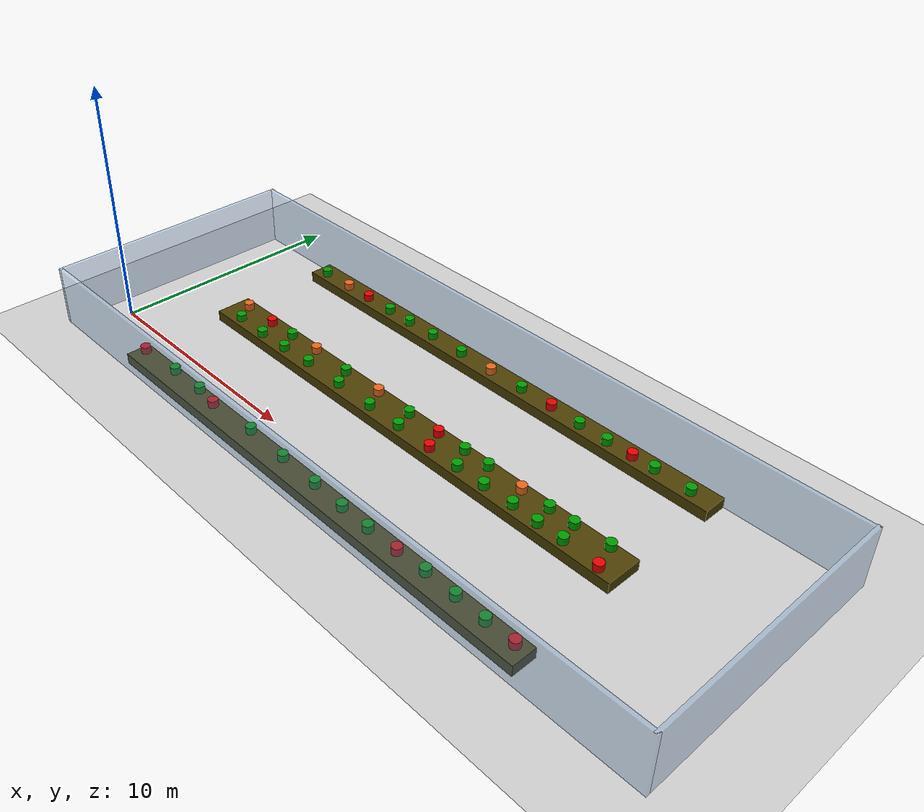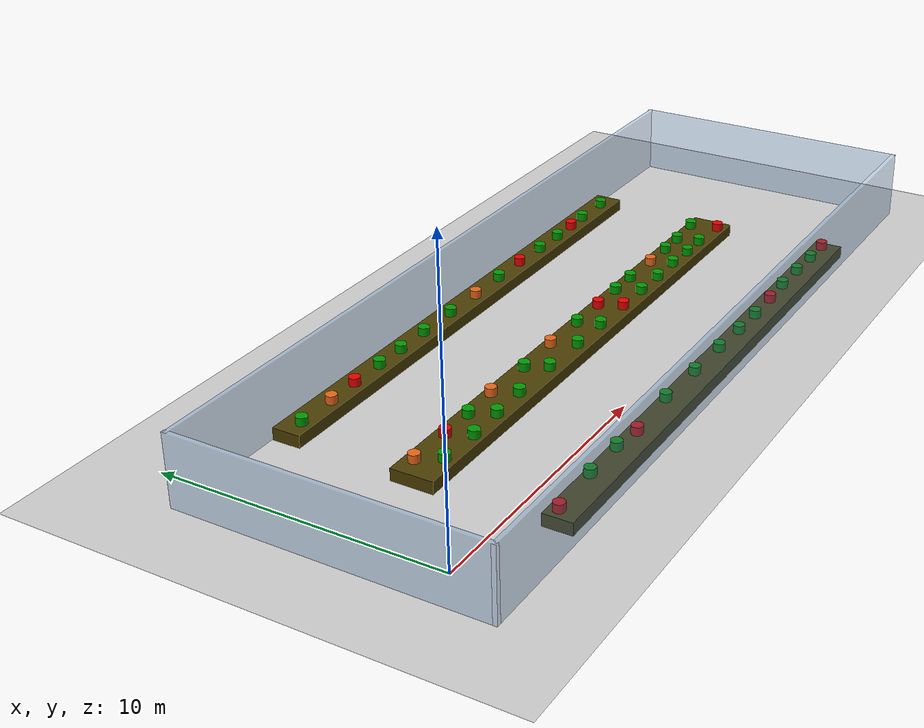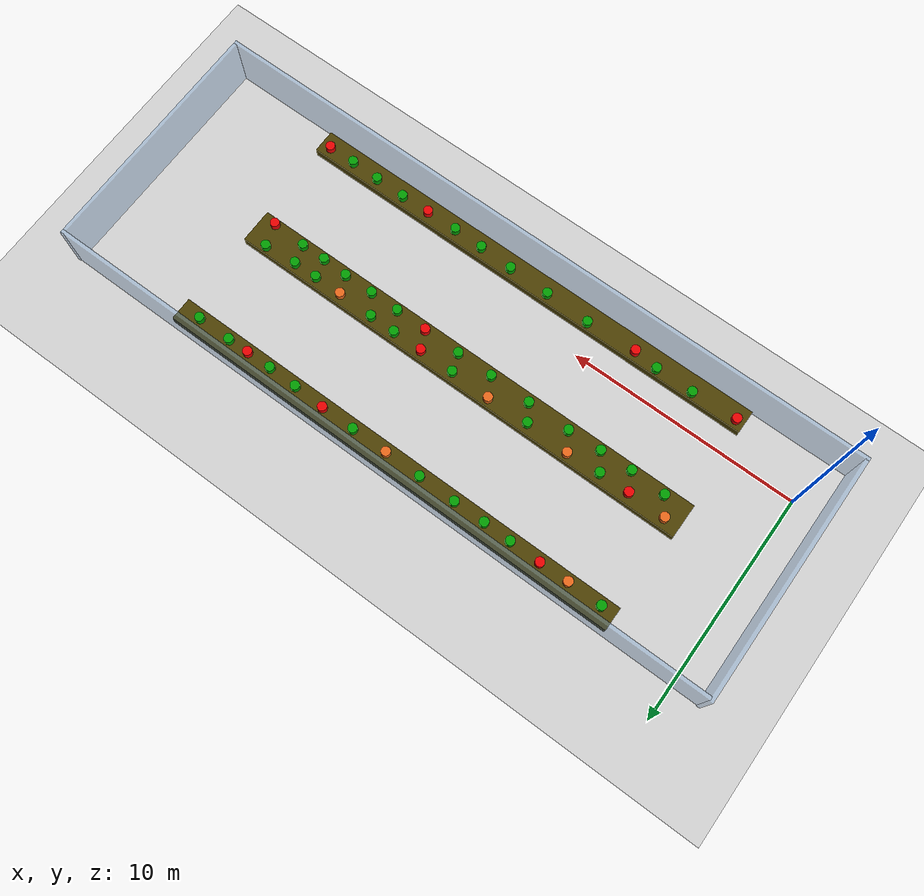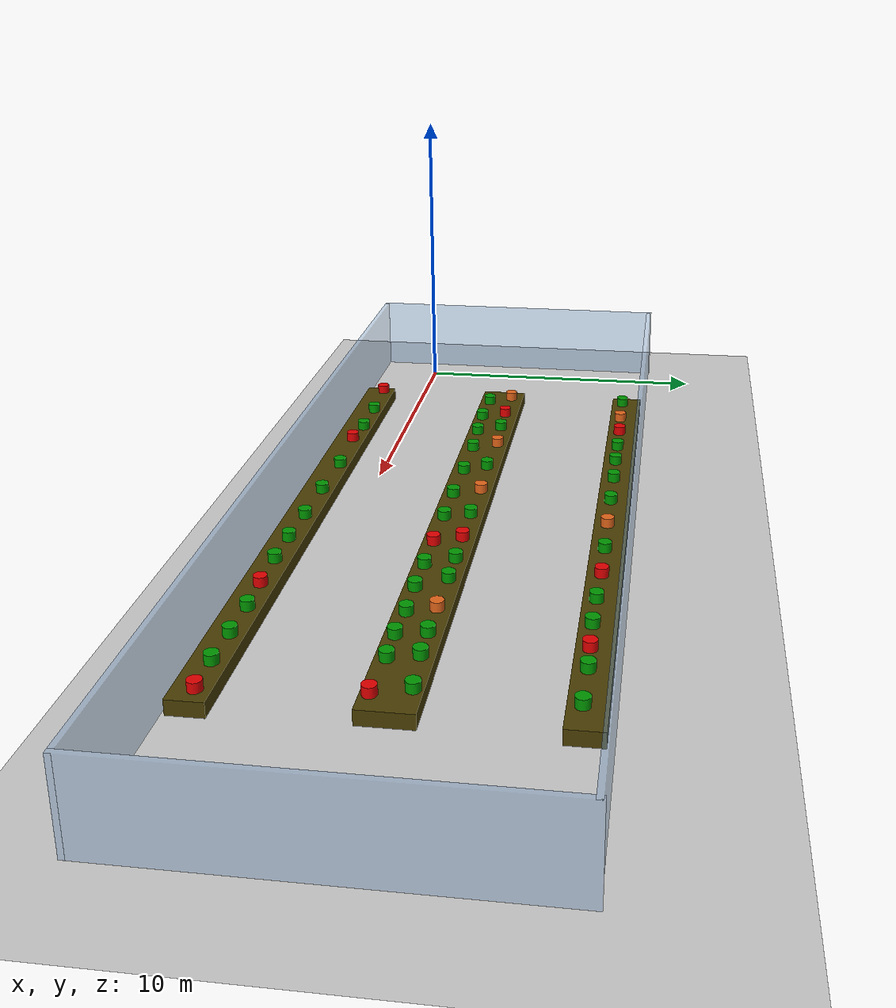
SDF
<sdf version="1.7">
 <world name="default">
  <light name="sun" type="directional">
   <pose>0 0 10 0 -0 0</pose>
   <diffuse>0.8 0.8 0.8 1</diffuse>
   <specular>0.2 0.2 0.2 1</specular>
   <attenuation>
    <range>1000</range>
    <constant>0.9</constant>
    <linear>0.01</linear>
    <quadratic>0.001</quadratic>
   </attenuation>
   <direction>-0.5 0.1 -0.9</direction>
   <spot><inner_angle>0</inner_angle><outer_angle>0</outer_angle><falloff>0</falloff></spot>
  </light>
  <model name="ground_plane">
   <static>1</static>
   <link name="link">
    <collision name="collision">
     <geometry><plane><normal>0 0 1</normal><size>100 100</size></plane></geometry>
     <surface><friction><ode><mu>100</mu><mu2>50</mu2></ode></friction></surface>
    </collision>
    <visual name="visual">
     <cast_shadows>0</cast_shadows>
     <geometry><plane><normal>0 0 1</normal><size>100 100</size></plane></geometry>
     <material>
      <script><uri>file://media/materials/scripts/gazebo.material</uri><name>Gazebo/Grey</name></script>
     </material>
    </visual>
   </link>
  </model>
  <gravity>0 0 -9.8</gravity>
  <magnetic_field>6e-06 2.3e-05 -4.2e-05</magnetic_field>
  <atmosphere type="adiabatic"/>
  <physics type="ode">
   <max_step_size>0.001</max_step_size>
   <real_time_factor>1</real_time_factor>
   <real_time_update_rate>1000</real_time_update_rate>
  </physics>
  <scene><ambient>0.4 0.4 0.4 1</ambient><background>0.7 0.7 0.7 1</background><shadows>1</shadows></scene>
  <spherical_coordinates>
   <surface_model>EARTH_WGS84</surface_model>
   <latitude_deg>0</latitude_deg>
   <longitude_deg>0</longitude_deg>
   <elevation>0</elevation>
   <heading_deg>0</heading_deg>
  </spherical_coordinates>
  <model name="Test_pot_green">
   <link name="link_0">
    <inertial>
     <mass>0.044841</mass>
     <inertia>
      <ixx>0.00074807</ixx>
      <ixy>0</ixy>
      <ixz>0</ixz>
      <iyy>0.00074807</iyy>
      <iyz>0</iyz>
      <izz>0.00086495</izz>
     </inertia>
    </inertial>
    <pose>3e-06 1e-06 0 0 -0 0</pose>
    <visual name="visual">
     <geometry><cylinder><radius>0.196415</radius><length>0.290612</length></cylinder></geometry>
     <material>
      <lighting>1</lighting>
      <script><uri>file://media/materials/scripts/gazebo.material</uri><name>Gazebo/Grey</name></script>
      <shader type="pixel"><normal_map>__default__</normal_map></shader>
      <diffuse>0 0.6 0 0</diffuse>
      <ambient>0.3 0.3 0.3 1</ambient>
      <specular>0.01 0.01 0.01 1</specular>
      <emissive>0 0 0 1</emissive>
     </material>
    </visual>
    <collision name="collision">
     <geometry><cylinder><radius>0.196415</radius><length>0.290612</length></cylinder></geometry>
     <surface>
      <friction>
       <ode><mu>1</mu><mu2>1</mu2><fdir1>0 0 0</fdir1><slip1>0</slip1><slip2>0</slip2></ode>
       <torsional>
        <coefficient>1</coefficient>
        <patch_radius>0</patch_radius>
        <surface_radius>0</surface_radius>
        <use_patch_radius>1</use_patch_radius>
        <ode><slip>0</slip></ode>
       </torsional>
      </friction>
      <bounce><restitution_coefficient>0</restitution_coefficient><threshold>1e+06</threshold></bounce>
      <contact>
       <collide_without_contact>0</collide_without_contact>
       <collide_without_contact_bitmask>1</collide_without_contact_bitmask>
       <collide_bitmask>1</collide_bitmask>
       <ode>
        <soft_cfm>0</soft_cfm>
        <soft_erp>0.2</soft_erp>
        <kp>1e+13</kp>
        <kd>1</kd>
        <max_vel>0.01</max_vel>
        <min_depth>0</min_depth>
       </ode>
       <bullet>
        <split_impulse>1</split_impulse>
        <split_impulse_penetration_threshold>-0.01</split_impulse_penetration_threshold>
        <soft_cfm>0</soft_cfm>
        <soft_erp>0.2</soft_erp>
        <kp>1e+13</kp>
        <kd>1</kd>
       </bullet>
      </contact>
     </surface>
    </collision>
   </link>
   <static>0</static>
   <pose>3.66478 7.67336 0.575569 3.5e-05 1e-06 -0.002797</pose>
  </model>
  <model name="Test_pot_red">
   <link name="link_0">
    <inertial>
     <mass>0.044841</mass>
     <inertia>
      <ixx>0.00074807</ixx>
      <ixy>0</ixy>
      <ixz>0</ixz>
      <iyy>0.00074807</iyy>
      <iyz>0</iyz>
      <izz>0.00086495</izz>
     </inertia>
    </inertial>
    <pose>3e-06 1e-06 -0 0 -0 0</pose>
    <visual name="visual">
     <geometry><cylinder><radius>0.196415</radius><length>0.290612</length></cylinder></geometry>
     <material>
      <lighting>1</lighting>
      <script><uri>file://media/materials/scripts/gazebo.material</uri><name>Gazebo/Grey</name></script>
      <shader type="pixel"><normal_map>__default__</normal_map></shader>
      <ambient>0.3 0.3 0.3 1</ambient>
      <diffuse>0.9 0 0 1</diffuse>
      <specular>0.01 0.01 0.01 1</specular>
      <emissive>0 0 0 1</emissive>
     </material>
    </visual>
    <collision name="collision">
     <geometry><cylinder><radius>0.196415</radius><length>0.290612</length></cylinder></geometry>
     <surface>
      <friction>
       <ode><mu>1</mu><mu2>1</mu2><fdir1>0 0 0</fdir1><slip1>0</slip1><slip2>0</slip2></ode>
       <torsional>
        <coefficient>1</coefficient>
        <patch_radius>0</patch_radius>
        <surface_radius>0</surface_radius>
        <use_patch_radius>1</use_patch_radius>
        <ode><slip>0</slip></ode>
       </torsional>
      </friction>
      <bounce><restitution_coefficient>0</restitution_coefficient><threshold>1e+06</threshold></bounce>
      <contact>
       <collide_without_contact>0</collide_without_contact>
       <collide_without_contact_bitmask>1</collide_without_contact_bitmask>
       <collide_bitmask>1</collide_bitmask>
       <ode>
        <soft_cfm>0</soft_cfm>
        <soft_erp>0.2</soft_erp>
        <kp>1e+13</kp>
        <kd>1</kd>
        <max_vel>0.01</max_vel>
        <min_depth>0</min_depth>
       </ode>
       <bullet>
        <split_impulse>1</split_impulse>
        <split_impulse_penetration_threshold>-0.01</split_impulse_penetration_threshold>
        <soft_cfm>0</soft_cfm>
        <soft_erp>0.2</soft_erp>
        <kp>1e+13</kp>
        <kd>1</kd>
       </bullet>
      </contact>
     </surface>
    </collision>
   </link>
   <static>0</static>
   <pose>6.40214 7.70189 0.575568 3e-06 1e-06 -0.004789</pose>
  </model>
  <model name="Test_pot_orange">
   <link name="link_0">
    <inertial>
     <mass>0.044841</mass>
     <inertia>
      <ixx>0.00074807</ixx>
      <ixy>0</ixy>
      <ixz>0</ixz>
      <iyy>0.00074807</iyy>
      <iyz>0</iyz>
      <izz>0.00086495</izz>
     </inertia>
    </inertial>
    <pose>3e-06 1e-06 -0 0 -0 0</pose>
    <visual name="visual">
     <geometry><cylinder><radius>0.196415</radius><length>0.290612</length></cylinder></geometry>
     <material>
      <lighting>1</lighting>
      <script><uri>file://media/materials/scripts/gazebo.material</uri><name>Gazebo/Grey</name></script>
      <shader type="pixel"><normal_map>__default__</normal_map></shader>
      <ambient>0.3 0.3 0.3 1</ambient>
      <diffuse>0.9 0.4 0.1 1</diffuse>
      <specular>0.01 0.01 0.01 1</specular>
      <emissive>0 0 0 1</emissive>
     </material>
    </visual>
    <collision name="collision">
     <geometry><cylinder><radius>0.196415</radius><length>0.290612</length></cylinder></geometry>
     <surface>
      <friction>
       <ode><mu>1</mu><mu2>1</mu2><fdir1>0 0 0</fdir1><slip1>0</slip1><slip2>0</slip2></ode>
       <torsional>
        <coefficient>1</coefficient>
        <patch_radius>0</patch_radius>
        <surface_radius>0</surface_radius>
        <use_patch_radius>1</use_patch_radius>
        <ode><slip>0</slip></ode>
       </torsional>
      </friction>
      <bounce><restitution_coefficient>0</restitution_coefficient><threshold>1e+06</threshold></bounce>
      <contact>
       <collide_without_contact>0</collide_without_contact>
       <collide_without_contact_bitmask>1</collide_without_contact_bitmask>
       <collide_bitmask>1</collide_bitmask>
       <ode>
        <soft_cfm>0</soft_cfm>
        <soft_erp>0.2</soft_erp>
        <kp>1e+13</kp>
        <kd>1</kd>
        <max_vel>0.01</max_vel>
        <min_depth>0</min_depth>
       </ode>
       <bullet>
        <split_impulse>1</split_impulse>
        <split_impulse_penetration_threshold>-0.01</split_impulse_penetration_threshold>
        <soft_cfm>0</soft_cfm>
        <soft_erp>0.2</soft_erp>
        <kp>1e+13</kp>
        <kd>1</kd>
       </bullet>
      </contact>
     </surface>
    </collision>
   </link>
   <static>0</static>
   <pose>5.14852 7.66622 0.575578 -3.6e-05 -4e-06 -0.002668</pose>
  </model>
  <model name="Test_pot_green_clone">
   <link name="link_0">
    <inertial>
     <mass>0.044841</mass>
     <inertia>
      <ixx>0.00074807</ixx>
      <ixy>0</ixy>
      <ixz>0</ixz>
      <iyy>0.00074807</iyy>
      <iyz>0</iyz>
      <izz>0.00086495</izz>
     </inertia>
    </inertial>
    <pose>3e-06 1e-06 0 0 -0 0</pose>
    <visual name="visual">
     <geometry><cylinder><radius>0.196415</radius><length>0.290612</length></cylinder></geometry>
     <material>
      <lighting>1</lighting>
      <script><uri>file://media/materials/scripts/gazebo.material</uri><name>Gazebo/Grey</name></script>
      <shader type="pixel"><normal_map>__default__</normal_map></shader>
      <diffuse>0 0.6 0 0</diffuse>
      <ambient>0.3 0.3 0.3 1</ambient>
      <specular>0.01 0.01 0.01 1</specular>
      <emissive>0 0 0 1</emissive>
     </material>
    </visual>
    <collision name="collision">
     <geometry><cylinder><radius>0.196415</radius><length>0.290612</length></cylinder></geometry>
     <surface>
      <friction>
       <ode><mu>1</mu><mu2>1</mu2><fdir1>0 0 0</fdir1><slip1>0</slip1><slip2>0</slip2></ode>
       <torsional>
        <coefficient>1</coefficient>
        <patch_radius>0</patch_radius>
        <surface_radius>0</surface_radius>
        <use_patch_radius>1</use_patch_radius>
        <ode><slip>0</slip></ode>
       </torsional>
      </friction>
      <bounce><restitution_coefficient>0</restitution_coefficient><threshold>1e+06</threshold></bounce>
      <contact>
       <collide_without_contact>0</collide_without_contact>
       <collide_without_contact_bitmask>1</collide_without_contact_bitmask>
       <collide_bitmask>1</collide_bitmask>
       <ode>
        <soft_cfm>0</soft_cfm>
        <soft_erp>0.2</soft_erp>
        <kp>1e+13</kp>
        <kd>1</kd>
        <max_vel>0.01</max_vel>
        <min_depth>0</min_depth>
       </ode>
       <bullet>
        <split_impulse>1</split_impulse>
        <split_impulse_penetration_threshold>-0.01</split_impulse_penetration_threshold>
        <soft_cfm>0</soft_cfm>
        <soft_erp>0.2</soft_erp>
        <kp>1e+13</kp>
        <kd>1</kd>
       </bullet>
      </contact>
     </surface>
    </collision>
   </link>
   <static>0</static>
   <pose>7.74714 7.70175 0.575592 1.6e-05 5e-06 0.000895</pose>
  </model>
  <model name="Test_pot_green_clone_0">
   <link name="link_0">
    <inertial>
     <mass>0.044841</mass>
     <inertia>
      <ixx>0.00074807</ixx>
      <ixy>0</ixy>
      <ixz>0</ixz>
      <iyy>0.00074807</iyy>
      <iyz>0</iyz>
      <izz>0.00086495</izz>
     </inertia>
    </inertial>
    <pose>3e-06 1e-06 0 0 -0 0</pose>
    <visual name="visual">
     <geometry><cylinder><radius>0.196415</radius><length>0.290612</length></cylinder></geometry>
     <material>
      <lighting>1</lighting>
      <script><uri>file://media/materials/scripts/gazebo.material</uri><name>Gazebo/Grey</name></script>
      <shader type="pixel"><normal_map>__default__</normal_map></shader>
      <diffuse>0 0.6 0 0</diffuse>
      <ambient>0.3 0.3 0.3 1</ambient>
      <specular>0.01 0.01 0.01 1</specular>
      <emissive>0 0 0 1</emissive>
     </material>
    </visual>
    <collision name="collision">
     <geometry><cylinder><radius>0.196415</radius><length>0.290612</length></cylinder></geometry>
     <surface>
      <friction>
       <ode><mu>1</mu><mu2>1</mu2><fdir1>0 0 0</fdir1><slip1>0</slip1><slip2>0</slip2></ode>
       <torsional>
        <coefficient>1</coefficient>
        <patch_radius>0</patch_radius>
        <surface_radius>0</surface_radius>
        <use_patch_radius>1</use_patch_radius>
        <ode><slip>0</slip></ode>
       </torsional>
      </friction>
      <bounce><restitution_coefficient>0</restitution_coefficient><threshold>1e+06</threshold></bounce>
      <contact>
       <collide_without_contact>0</collide_without_contact>
       <collide_without_contact_bitmask>1</collide_without_contact_bitmask>
       <collide_bitmask>1</collide_bitmask>
       <ode>
        <soft_cfm>0</soft_cfm>
        <soft_erp>0.2</soft_erp>
        <kp>1e+13</kp>
        <kd>1</kd>
        <max_vel>0.01</max_vel>
        <min_depth>0</min_depth>
       </ode>
       <bullet>
        <split_impulse>1</split_impulse>
        <split_impulse_penetration_threshold>-0.01</split_impulse_penetration_threshold>
        <soft_cfm>0</soft_cfm>
        <soft_erp>0.2</soft_erp>
        <kp>1e+13</kp>
        <kd>1</kd>
       </bullet>
      </contact>
     </surface>
    </collision>
   </link>
   <static>0</static>
   <pose>8.95 7.70055 0.575573 -2.3e-05 -2e-06 -0.001644</pose>
  </model>
  <model name="Test_pot_green_clone_1">
   <link name="link_0">
    <inertial>
     <mass>0.044841</mass>
     <inertia>
      <ixx>0.00074807</ixx>
      <ixy>0</ixy>
      <ixz>0</ixz>
      <iyy>0.00074807</iyy>
      <iyz>0</iyz>
      <izz>0.00086495</izz>
     </inertia>
    </inertial>
    <pose>3e-06 1e-06 0 0 -0 0</pose>
    <visual name="visual">
     <geometry><cylinder><radius>0.196415</radius><length>0.290612</length></cylinder></geometry>
     <material>
      <lighting>1</lighting>
      <script><uri>file://media/materials/scripts/gazebo.material</uri><name>Gazebo/Grey</name></script>
      <shader type="pixel"><normal_map>__default__</normal_map></shader>
      <diffuse>0 0.6 0 0</diffuse>
      <ambient>0.3 0.3 0.3 1</ambient>
      <specular>0.01 0.01 0.01 1</specular>
      <emissive>0 0 0 1</emissive>
     </material>
    </visual>
    <collision name="collision">
     <geometry><cylinder><radius>0.196415</radius><length>0.290612</length></cylinder></geometry>
     <surface>
      <friction>
       <ode><mu>1</mu><mu2>1</mu2><fdir1>0 0 0</fdir1><slip1>0</slip1><slip2>0</slip2></ode>
       <torsional>
        <coefficient>1</coefficient>
        <patch_radius>0</patch_radius>
        <surface_radius>0</surface_radius>
        <use_patch_radius>1</use_patch_radius>
        <ode><slip>0</slip></ode>
       </torsional>
      </friction>
      <bounce><restitution_coefficient>0</restitution_coefficient><threshold>1e+06</threshold></bounce>
      <contact>
       <collide_without_contact>0</collide_without_contact>
       <collide_without_contact_bitmask>1</collide_without_contact_bitmask>
       <collide_bitmask>1</collide_bitmask>
       <ode>
        <soft_cfm>0</soft_cfm>
        <soft_erp>0.2</soft_erp>
        <kp>1e+13</kp>
        <kd>1</kd>
        <max_vel>0.01</max_vel>
        <min_depth>0</min_depth>
       </ode>
       <bullet>
        <split_impulse>1</split_impulse>
        <split_impulse_penetration_threshold>-0.01</split_impulse_penetration_threshold>
        <soft_cfm>0</soft_cfm>
        <soft_erp>0.2</soft_erp>
        <kp>1e+13</kp>
        <kd>1</kd>
       </bullet>
      </contact>
     </surface>
    </collision>
   </link>
   <static>0</static>
   <pose>10.3223 7.71373 0.575575 -3e-05 -5e-06 -0.004784</pose>
  </model>
  <model name="Test_pot_green_clone_2">
   <link name="link_0">
    <inertial>
     <mass>0.044841</mass>
     <inertia>
      <ixx>0.00074807</ixx>
      <ixy>0</ixy>
      <ixz>0</ixz>
      <iyy>0.00074807</iyy>
      <iyz>0</iyz>
      <izz>0.00086495</izz>
     </inertia>
    </inertial>
    <pose>3e-06 1e-06 0 0 -0 0</pose>
    <visual name="visual">
     <geometry><cylinder><radius>0.196415</radius><length>0.290612</length></cylinder></geometry>
     <material>
      <lighting>1</lighting>
      <script><uri>file://media/materials/scripts/gazebo.material</uri><name>Gazebo/Grey</name></script>
      <shader type="pixel"><normal_map>__default__</normal_map></shader>
      <diffuse>0 0.6 0 0</diffuse>
      <ambient>0.3 0.3 0.3 1</ambient>
      <specular>0.01 0.01 0.01 1</specular>
      <emissive>0 0 0 1</emissive>
     </material>
    </visual>
    <collision name="collision">
     <geometry><cylinder><radius>0.196415</radius><length>0.290612</length></cylinder></geometry>
     <surface>
      <friction>
       <ode><mu>1</mu><mu2>1</mu2><fdir1>0 0 0</fdir1><slip1>0</slip1><slip2>0</slip2></ode>
       <torsional>
        <coefficient>1</coefficient>
        <patch_radius>0</patch_radius>
        <surface_radius>0</surface_radius>
        <use_patch_radius>1</use_patch_radius>
        <ode><slip>0</slip></ode>
       </torsional>
      </friction>
      <bounce><restitution_coefficient>0</restitution_coefficient><threshold>1e+06</threshold></bounce>
      <contact>
       <collide_without_contact>0</collide_without_contact>
       <collide_without_contact_bitmask>1</collide_without_contact_bitmask>
       <collide_bitmask>1</collide_bitmask>
       <ode>
        <soft_cfm>0</soft_cfm>
        <soft_erp>0.2</soft_erp>
        <kp>1e+13</kp>
        <kd>1</kd>
        <max_vel>0.01</max_vel>
        <min_depth>0</min_depth>
       </ode>
       <bullet>
        <split_impulse>1</split_impulse>
        <split_impulse_penetration_threshold>-0.01</split_impulse_penetration_threshold>
        <soft_cfm>0</soft_cfm>
        <soft_erp>0.2</soft_erp>
        <kp>1e+13</kp>
        <kd>1</kd>
       </bullet>
      </contact>
     </surface>
    </collision>
   </link>
   <static>0</static>
   <pose>11.96 7.71035 0.575578 4.9e-05 1e-06 -0.004177</pose>
  </model>
  <model name="Test_pot_green_clone_3">
   <link name="link_0">
    <inertial>
     <mass>0.044841</mass>
     <inertia>
      <ixx>0.00074807</ixx>
      <ixy>0</ixy>
      <ixz>0</ixz>
      <iyy>0.00074807</iyy>
      <iyz>0</iyz>
      <izz>0.00086495</izz>
     </inertia>
    </inertial>
    <pose>3e-06 1e-06 0 0 -0 0</pose>
    <visual name="visual">
     <geometry><cylinder><radius>0.196415</radius><length>0.290612</length></cylinder></geometry>
     <material>
      <lighting>1</lighting>
      <script><uri>file://media/materials/scripts/gazebo.material</uri><name>Gazebo/Grey</name></script>
      <shader type="pixel"><normal_map>__default__</normal_map></shader>
      <diffuse>0 0.6 0 0</diffuse>
      <ambient>0.3 0.3 0.3 1</ambient>
      <specular>0.01 0.01 0.01 1</specular>
      <emissive>0 0 0 1</emissive>
     </material>
    </visual>
    <collision name="collision">
     <geometry><cylinder><radius>0.196415</radius><length>0.290612</length></cylinder></geometry>
     <surface>
      <friction>
       <ode><mu>1</mu><mu2>1</mu2><fdir1>0 0 0</fdir1><slip1>0</slip1><slip2>0</slip2></ode>
       <torsional>
        <coefficient>1</coefficient>
        <patch_radius>0</patch_radius>
        <surface_radius>0</surface_radius>
        <use_patch_radius>1</use_patch_radius>
        <ode><slip>0</slip></ode>
       </torsional>
      </friction>
      <bounce><restitution_coefficient>0</restitution_coefficient><threshold>1e+06</threshold></bounce>
      <contact>
       <collide_without_contact>0</collide_without_contact>
       <collide_without_contact_bitmask>1</collide_without_contact_bitmask>
       <collide_bitmask>1</collide_bitmask>
       <ode>
        <soft_cfm>0</soft_cfm>
        <soft_erp>0.2</soft_erp>
        <kp>1e+13</kp>
        <kd>1</kd>
        <max_vel>0.01</max_vel>
        <min_depth>0</min_depth>
       </ode>
       <bullet>
        <split_impulse>1</split_impulse>
        <split_impulse_penetration_threshold>-0.01</split_impulse_penetration_threshold>
        <soft_cfm>0</soft_cfm>
        <soft_erp>0.2</soft_erp>
        <kp>1e+13</kp>
        <kd>1</kd>
       </bullet>
      </contact>
     </surface>
    </collision>
   </link>
   <static>0</static>
   <pose>15.1495 7.72388 0.575568 7e-06 -4e-06 -0.002778</pose>
  </model>
  <model name="Test_pot_green_clone_4">
   <link name="link_0">
    <inertial>
     <mass>0.044841</mass>
     <inertia>
      <ixx>0.00074807</ixx>
      <ixy>0</ixy>
      <ixz>0</ixz>
      <iyy>0.00074807</iyy>
      <iyz>0</iyz>
      <izz>0.00086495</izz>
     </inertia>
    </inertial>
    <pose>3e-06 1e-06 0 0 -0 0</pose>
    <visual name="visual">
     <geometry><cylinder><radius>0.196415</radius><length>0.290612</length></cylinder></geometry>
     <material>
      <lighting>1</lighting>
      <script><uri>file://media/materials/scripts/gazebo.material</uri><name>Gazebo/Grey</name></script>
      <shader type="pixel"><normal_map>__default__</normal_map></shader>
      <diffuse>0 0.6 0 0</diffuse>
      <ambient>0.3 0.3 0.3 1</ambient>
      <specular>0.01 0.01 0.01 1</specular>
      <emissive>0 0 0 1</emissive>
     </material>
    </visual>
    <collision name="collision">
     <geometry><cylinder><radius>0.196415</radius><length>0.290612</length></cylinder></geometry>
     <surface>
      <friction>
       <ode><mu>1</mu><mu2>1</mu2><fdir1>0 0 0</fdir1><slip1>0</slip1><slip2>0</slip2></ode>
       <torsional>
        <coefficient>1</coefficient>
        <patch_radius>0</patch_radius>
        <surface_radius>0</surface_radius>
        <use_patch_radius>1</use_patch_radius>
        <ode><slip>0</slip></ode>
       </torsional>
      </friction>
      <bounce><restitution_coefficient>0</restitution_coefficient><threshold>1e+06</threshold></bounce>
      <contact>
       <collide_without_contact>0</collide_without_contact>
       <collide_without_contact_bitmask>1</collide_without_contact_bitmask>
       <collide_bitmask>1</collide_bitmask>
       <ode>
        <soft_cfm>0</soft_cfm>
        <soft_erp>0.2</soft_erp>
        <kp>1e+13</kp>
        <kd>1</kd>
        <max_vel>0.01</max_vel>
        <min_depth>0</min_depth>
       </ode>
       <bullet>
        <split_impulse>1</split_impulse>
        <split_impulse_penetration_threshold>-0.01</split_impulse_penetration_threshold>
        <soft_cfm>0</soft_cfm>
        <soft_erp>0.2</soft_erp>
        <kp>1e+13</kp>
        <kd>1</kd>
       </bullet>
      </contact>
     </surface>
    </collision>
   </link>
   <static>0</static>
   <pose>18.0132 7.68148 0.575581 0 3e-06 0.002291</pose>
  </model>
  <model name="Test_pot_green_clone_5">
   <link name="link_0">
    <inertial>
     <mass>0.044841</mass>
     <inertia>
      <ixx>0.00074807</ixx>
      <ixy>0</ixy>
      <ixz>0</ixz>
      <iyy>0.00074807</iyy>
      <iyz>0</iyz>
      <izz>0.00086495</izz>
     </inertia>
    </inertial>
    <pose>3e-06 1e-06 0 0 -0 0</pose>
    <visual name="visual">
     <geometry><cylinder><radius>0.196415</radius><length>0.290612</length></cylinder></geometry>
     <material>
      <lighting>1</lighting>
      <script><uri>file://media/materials/scripts/gazebo.material</uri><name>Gazebo/Grey</name></script>
      <shader type="pixel"><normal_map>__default__</normal_map></shader>
      <diffuse>0 0.6 0 0</diffuse>
      <ambient>0.3 0.3 0.3 1</ambient>
      <specular>0.01 0.01 0.01 1</specular>
      <emissive>0 0 0 1</emissive>
     </material>
    </visual>
    <collision name="collision">
     <geometry><cylinder><radius>0.196415</radius><length>0.290612</length></cylinder></geometry>
     <surface>
      <friction>
       <ode><mu>1</mu><mu2>1</mu2><fdir1>0 0 0</fdir1><slip1>0</slip1><slip2>0</slip2></ode>
       <torsional>
        <coefficient>1</coefficient>
        <patch_radius>0</patch_radius>
        <surface_radius>0</surface_radius>
        <use_patch_radius>1</use_patch_radius>
        <ode><slip>0</slip></ode>
       </torsional>
      </friction>
      <bounce><restitution_coefficient>0</restitution_coefficient><threshold>1e+06</threshold></bounce>
      <contact>
       <collide_without_contact>0</collide_without_contact>
       <collide_without_contact_bitmask>1</collide_without_contact_bitmask>
       <collide_bitmask>1</collide_bitmask>
       <ode>
        <soft_cfm>0</soft_cfm>
        <soft_erp>0.2</soft_erp>
        <kp>1e+13</kp>
        <kd>1</kd>
        <max_vel>0.01</max_vel>
        <min_depth>0</min_depth>
       </ode>
       <bullet>
        <split_impulse>1</split_impulse>
        <split_impulse_penetration_threshold>-0.01</split_impulse_penetration_threshold>
        <soft_cfm>0</soft_cfm>
        <soft_erp>0.2</soft_erp>
        <kp>1e+13</kp>
        <kd>1</kd>
       </bullet>
      </contact>
     </surface>
    </collision>
   </link>
   <static>0</static>
   <pose>19.2874 7.66309 0.575572 1.1e-05 -1e-06 0.001082</pose>
  </model>
  <model name="Test_pot_green_clone_6">
   <link name="link_0">
    <inertial>
     <mass>0.044841</mass>
     <inertia>
      <ixx>0.00074807</ixx>
      <ixy>0</ixy>
      <ixz>0</ixz>
      <iyy>0.00074807</iyy>
      <iyz>0</iyz>
      <izz>0.00086495</izz>
     </inertia>
    </inertial>
    <pose>3e-06 1e-06 0 0 -0 0</pose>
    <visual name="visual">
     <geometry><cylinder><radius>0.196415</radius><length>0.290612</length></cylinder></geometry>
     <material>
      <lighting>1</lighting>
      <script><uri>file://media/materials/scripts/gazebo.material</uri><name>Gazebo/Grey</name></script>
      <shader type="pixel"><normal_map>__default__</normal_map></shader>
      <diffuse>0 0.6 0 0</diffuse>
      <ambient>0.3 0.3 0.3 1</ambient>
      <specular>0.01 0.01 0.01 1</specular>
      <emissive>0 0 0 1</emissive>
     </material>
    </visual>
    <collision name="collision">
     <geometry><cylinder><radius>0.196415</radius><length>0.290612</length></cylinder></geometry>
     <surface>
      <friction>
       <ode><mu>1</mu><mu2>1</mu2><fdir1>0 0 0</fdir1><slip1>0</slip1><slip2>0</slip2></ode>
       <torsional>
        <coefficient>1</coefficient>
        <patch_radius>0</patch_radius>
        <surface_radius>0</surface_radius>
        <use_patch_radius>1</use_patch_radius>
        <ode><slip>0</slip></ode>
       </torsional>
      </friction>
      <bounce><restitution_coefficient>0</restitution_coefficient><threshold>1e+06</threshold></bounce>
      <contact>
       <collide_without_contact>0</collide_without_contact>
       <collide_without_contact_bitmask>1</collide_without_contact_bitmask>
       <collide_bitmask>1</collide_bitmask>
       <ode>
        <soft_cfm>0</soft_cfm>
        <soft_erp>0.2</soft_erp>
        <kp>1e+13</kp>
        <kd>1</kd>
        <max_vel>0.01</max_vel>
        <min_depth>0</min_depth>
       </ode>
       <bullet>
        <split_impulse>1</split_impulse>
        <split_impulse_penetration_threshold>-0.01</split_impulse_penetration_threshold>
        <soft_cfm>0</soft_cfm>
        <soft_erp>0.2</soft_erp>
        <kp>1e+13</kp>
        <kd>1</kd>
       </bullet>
      </contact>
     </surface>
    </collision>
   </link>
   <static>0</static>
   <pose>21.3341 7.70057 0.57559 -3.4e-05 -2e-06 0.000809</pose>
  </model>
  <model name="Test_pot_green_clone_7">
   <link name="link_0">
    <inertial>
     <mass>0.044841</mass>
     <inertia>
      <ixx>0.00074807</ixx>
      <ixy>0</ixy>
      <ixz>0</ixz>
      <iyy>0.00074807</iyy>
      <iyz>0</iyz>
      <izz>0.00086495</izz>
     </inertia>
    </inertial>
    <pose>3e-06 1e-06 0 0 -0 0</pose>
    <visual name="visual">
     <geometry><cylinder><radius>0.196415</radius><length>0.290612</length></cylinder></geometry>
     <material>
      <lighting>1</lighting>
      <script><uri>file://media/materials/scripts/gazebo.material</uri><name>Gazebo/Grey</name></script>
      <shader type="pixel"><normal_map>__default__</normal_map></shader>
      <diffuse>0 0.6 0 0</diffuse>
      <ambient>0.3 0.3 0.3 1</ambient>
      <specular>0.01 0.01 0.01 1</specular>
      <emissive>0 0 0 1</emissive>
     </material>
    </visual>
    <collision name="collision">
     <geometry><cylinder><radius>0.196415</radius><length>0.290612</length></cylinder></geometry>
     <surface>
      <friction>
       <ode><mu>1</mu><mu2>1</mu2><fdir1>0 0 0</fdir1><slip1>0</slip1><slip2>0</slip2></ode>
       <torsional>
        <coefficient>1</coefficient>
        <patch_radius>0</patch_radius>
        <surface_radius>0</surface_radius>
        <use_patch_radius>1</use_patch_radius>
        <ode><slip>0</slip></ode>
       </torsional>
      </friction>
      <bounce><restitution_coefficient>0</restitution_coefficient><threshold>1e+06</threshold></bounce>
      <contact>
       <collide_without_contact>0</collide_without_contact>
       <collide_without_contact_bitmask>1</collide_without_contact_bitmask>
       <collide_bitmask>1</collide_bitmask>
       <ode>
        <soft_cfm>0</soft_cfm>
        <soft_erp>0.2</soft_erp>
        <kp>1e+13</kp>
        <kd>1</kd>
        <max_vel>0.01</max_vel>
        <min_depth>0</min_depth>
       </ode>
       <bullet>
        <split_impulse>1</split_impulse>
        <split_impulse_penetration_threshold>-0.01</split_impulse_penetration_threshold>
        <soft_cfm>0</soft_cfm>
        <soft_erp>0.2</soft_erp>
        <kp>1e+13</kp>
        <kd>1</kd>
       </bullet>
      </contact>
     </surface>
    </collision>
   </link>
   <static>0</static>
   <pose>22.8379 7.69095 0.575568 3.2e-05 -1e-06 0.003549</pose>
  </model>
  <model name="Test_pot_orange_clone">
   <link name="link_0">
    <inertial>
     <mass>0.044841</mass>
     <inertia>
      <ixx>0.00074807</ixx>
      <ixy>0</ixy>
      <ixz>0</ixz>
      <iyy>0.00074807</iyy>
      <iyz>0</iyz>
      <izz>0.00086495</izz>
     </inertia>
    </inertial>
    <pose>3e-06 1e-06 -0 0 -0 0</pose>
    <visual name="visual">
     <geometry><cylinder><radius>0.196415</radius><length>0.290612</length></cylinder></geometry>
     <material>
      <lighting>1</lighting>
      <script><uri>file://media/materials/scripts/gazebo.material</uri><name>Gazebo/Grey</name></script>
      <shader type="pixel"><normal_map>__default__</normal_map></shader>
      <ambient>0.3 0.3 0.3 1</ambient>
      <diffuse>0.9 0.4 0.1 1</diffuse>
      <specular>0.01 0.01 0.01 1</specular>
      <emissive>0 0 0 1</emissive>
     </material>
    </visual>
    <collision name="collision">
     <geometry><cylinder><radius>0.196415</radius><length>0.290612</length></cylinder></geometry>
     <surface>
      <friction>
       <ode><mu>1</mu><mu2>1</mu2><fdir1>0 0 0</fdir1><slip1>0</slip1><slip2>0</slip2></ode>
       <torsional>
        <coefficient>1</coefficient>
        <patch_radius>0</patch_radius>
        <surface_radius>0</surface_radius>
        <use_patch_radius>1</use_patch_radius>
        <ode><slip>0</slip></ode>
       </torsional>
      </friction>
      <bounce><restitution_coefficient>0</restitution_coefficient><threshold>1e+06</threshold></bounce>
      <contact>
       <collide_without_contact>0</collide_without_contact>
       <collide_without_contact_bitmask>1</collide_without_contact_bitmask>
       <collide_bitmask>1</collide_bitmask>
       <ode>
        <soft_cfm>0</soft_cfm>
        <soft_erp>0.2</soft_erp>
        <kp>1e+13</kp>
        <kd>1</kd>
        <max_vel>0.01</max_vel>
        <min_depth>0</min_depth>
       </ode>
       <bullet>
        <split_impulse>1</split_impulse>
        <split_impulse_penetration_threshold>-0.01</split_impulse_penetration_threshold>
        <soft_cfm>0</soft_cfm>
        <soft_erp>0.2</soft_erp>
        <kp>1e+13</kp>
        <kd>1</kd>
       </bullet>
      </contact>
     </surface>
    </collision>
   </link>
   <static>0</static>
   <pose>13.5652 7.70667 0.57557 -3e-06 -2e-06 -0.00832</pose>
  </model>
  <model name="Test_pot_orange_clone_0">
   <link name="link_0">
    <inertial>
     <mass>0.044841</mass>
     <inertia>
      <ixx>0.00074807</ixx>
      <ixy>0</ixy>
      <ixz>0</ixz>
      <iyy>0.00074807</iyy>
      <iyz>0</iyz>
      <izz>0.00086495</izz>
     </inertia>
    </inertial>
    <pose>3e-06 1e-06 -0 0 -0 0</pose>
    <visual name="visual">
     <geometry><cylinder><radius>0.196415</radius><length>0.290612</length></cylinder></geometry>
     <material>
      <lighting>1</lighting>
      <script><uri>file://media/materials/scripts/gazebo.material</uri><name>Gazebo/Grey</name></script>
      <shader type="pixel"><normal_map>__default__</normal_map></shader>
      <ambient>0.3 0.3 0.3 1</ambient>
      <diffuse>0.9 0.4 0.1 1</diffuse>
      <specular>0.01 0.01 0.01 1</specular>
      <emissive>0 0 0 1</emissive>
     </material>
    </visual>
    <collision name="collision">
     <geometry><cylinder><radius>0.196415</radius><length>0.290612</length></cylinder></geometry>
     <surface>
      <friction>
       <ode><mu>1</mu><mu2>1</mu2><fdir1>0 0 0</fdir1><slip1>0</slip1><slip2>0</slip2></ode>
       <torsional>
        <coefficient>1</coefficient>
        <patch_radius>0</patch_radius>
        <surface_radius>0</surface_radius>
        <use_patch_radius>1</use_patch_radius>
        <ode><slip>0</slip></ode>
       </torsional>
      </friction>
      <bounce><restitution_coefficient>0</restitution_coefficient><threshold>1e+06</threshold></bounce>
      <contact>
       <collide_without_contact>0</collide_without_contact>
       <collide_without_contact_bitmask>1</collide_without_contact_bitmask>
       <collide_bitmask>1</collide_bitmask>
       <ode>
        <soft_cfm>0</soft_cfm>
        <soft_erp>0.2</soft_erp>
        <kp>1e+13</kp>
        <kd>1</kd>
        <max_vel>0.01</max_vel>
        <min_depth>0</min_depth>
       </ode>
       <bullet>
        <split_impulse>1</split_impulse>
        <split_impulse_penetration_threshold>-0.01</split_impulse_penetration_threshold>
        <soft_cfm>0</soft_cfm>
        <soft_erp>0.2</soft_erp>
        <kp>1e+13</kp>
        <kd>1</kd>
       </bullet>
      </contact>
     </surface>
    </collision>
   </link>
   <static>0</static>
   <pose>3.59683 3.54736 0.57558 -1.1e-05 1e-06 -9e-06</pose>
  </model>
  <model name="Test_pot_orange_clone_1">
   <link name="link_0">
    <inertial>
     <mass>0.044841</mass>
     <inertia>
      <ixx>0.00074807</ixx>
      <ixy>0</ixy>
      <ixz>0</ixz>
      <iyy>0.00074807</iyy>
      <iyz>0</iyz>
      <izz>0.00086495</izz>
     </inertia>
    </inertial>
    <pose>3e-06 1e-06 -0 0 -0 0</pose>
    <visual name="visual">
     <geometry><cylinder><radius>0.196415</radius><length>0.290612</length></cylinder></geometry>
     <material>
      <lighting>1</lighting>
      <script><uri>file://media/materials/scripts/gazebo.material</uri><name>Gazebo/Grey</name></script>
      <shader type="pixel"><normal_map>__default__</normal_map></shader>
      <ambient>0.3 0.3 0.3 1</ambient>
      <diffuse>0.9 0.4 0.1 1</diffuse>
      <specular>0.01 0.01 0.01 1</specular>
      <emissive>0 0 0 1</emissive>
     </material>
    </visual>
    <collision name="collision">
     <geometry><cylinder><radius>0.196415</radius><length>0.290612</length></cylinder></geometry>
     <surface>
      <friction>
       <ode><mu>1</mu><mu2>1</mu2><fdir1>0 0 0</fdir1><slip1>0</slip1><slip2>0</slip2></ode>
       <torsional>
        <coefficient>1</coefficient>
        <patch_radius>0</patch_radius>
        <surface_radius>0</surface_radius>
        <use_patch_radius>1</use_patch_radius>
        <ode><slip>0</slip></ode>
       </torsional>
      </friction>
      <bounce><restitution_coefficient>0</restitution_coefficient><threshold>1e+06</threshold></bounce>
      <contact>
       <collide_without_contact>0</collide_without_contact>
       <collide_without_contact_bitmask>1</collide_without_contact_bitmask>
       <collide_bitmask>1</collide_bitmask>
       <ode>
        <soft_cfm>0</soft_cfm>
        <soft_erp>0.2</soft_erp>
        <kp>1e+13</kp>
        <kd>1</kd>
        <max_vel>0.01</max_vel>
        <min_depth>0</min_depth>
       </ode>
       <bullet>
        <split_impulse>1</split_impulse>
        <split_impulse_penetration_threshold>-0.01</split_impulse_penetration_threshold>
        <soft_cfm>0</soft_cfm>
        <soft_erp>0.2</soft_erp>
        <kp>1e+13</kp>
        <kd>1</kd>
       </bullet>
      </contact>
     </surface>
    </collision>
   </link>
   <static>0</static>
   <pose>7.97331 3.6356 0.575589 3.4e-05 -5e-06 0.005156</pose>
  </model>
  <model name="Test_pot_orange_clone_2">
   <link name="link_0">
    <inertial>
     <mass>0.044841</mass>
     <inertia>
      <ixx>0.00074807</ixx>
      <ixy>0</ixy>
      <ixz>0</ixz>
      <iyy>0.00074807</iyy>
      <iyz>0</iyz>
      <izz>0.00086495</izz>
     </inertia>
    </inertial>
    <pose>3e-06 1e-06 -0 0 -0 0</pose>
    <visual name="visual">
     <geometry><cylinder><radius>0.196415</radius><length>0.290612</length></cylinder></geometry>
     <material>
      <lighting>1</lighting>
      <script><uri>file://media/materials/scripts/gazebo.material</uri><name>Gazebo/Grey</name></script>
      <shader type="pixel"><normal_map>__default__</normal_map></shader>
      <ambient>0.3 0.3 0.3 1</ambient>
      <diffuse>0.9 0.4 0.1 1</diffuse>
      <specular>0.01 0.01 0.01 1</specular>
      <emissive>0 0 0 1</emissive>
     </material>
    </visual>
    <collision name="collision">
     <geometry><cylinder><radius>0.196415</radius><length>0.290612</length></cylinder></geometry>
     <surface>
      <friction>
       <ode><mu>1</mu><mu2>1</mu2><fdir1>0 0 0</fdir1><slip1>0</slip1><slip2>0</slip2></ode>
       <torsional>
        <coefficient>1</coefficient>
        <patch_radius>0</patch_radius>
        <surface_radius>0</surface_radius>
        <use_patch_radius>1</use_patch_radius>
        <ode><slip>0</slip></ode>
       </torsional>
      </friction>
      <bounce><restitution_coefficient>0</restitution_coefficient><threshold>1e+06</threshold></bounce>
      <contact>
       <collide_without_contact>0</collide_without_contact>
       <collide_without_contact_bitmask>1</collide_without_contact_bitmask>
       <collide_bitmask>1</collide_bitmask>
       <ode>
        <soft_cfm>0</soft_cfm>
        <soft_erp>0.2</soft_erp>
        <kp>1e+13</kp>
        <kd>1</kd>
        <max_vel>0.01</max_vel>
        <min_depth>0</min_depth>
       </ode>
       <bullet>
        <split_impulse>1</split_impulse>
        <split_impulse_penetration_threshold>-0.01</split_impulse_penetration_threshold>
        <soft_cfm>0</soft_cfm>
        <soft_erp>0.2</soft_erp>
        <kp>1e+13</kp>
        <kd>1</kd>
       </bullet>
      </contact>
     </surface>
    </collision>
   </link>
   <static>0</static>
   <pose>11.6959 3.62944 0.575588 3.2e-05 1e-06 0.000596</pose>
  </model>
  <model name="Test_pot_orange_clone_3">
   <link name="link_0">
    <inertial>
     <mass>0.044841</mass>
     <inertia>
      <ixx>0.00074807</ixx>
      <ixy>0</ixy>
      <ixz>0</ixz>
      <iyy>0.00074807</iyy>
      <iyz>0</iyz>
      <izz>0.00086495</izz>
     </inertia>
    </inertial>
    <pose>3e-06 1e-06 -0 0 -0 0</pose>
    <visual name="visual">
     <geometry><cylinder><radius>0.196415</radius><length>0.290612</length></cylinder></geometry>
     <material>
      <lighting>1</lighting>
      <script><uri>file://media/materials/scripts/gazebo.material</uri><name>Gazebo/Grey</name></script>
      <shader type="pixel"><normal_map>__default__</normal_map></shader>
      <ambient>0.3 0.3 0.3 1</ambient>
      <diffuse>0.9 0.4 0.1 1</diffuse>
      <specular>0.01 0.01 0.01 1</specular>
      <emissive>0 0 0 1</emissive>
     </material>
    </visual>
    <collision name="collision">
     <geometry><cylinder><radius>0.196415</radius><length>0.290612</length></cylinder></geometry>
     <surface>
      <friction>
       <ode><mu>1</mu><mu2>1</mu2><fdir1>0 0 0</fdir1><slip1>0</slip1><slip2>0</slip2></ode>
       <torsional>
        <coefficient>1</coefficient>
        <patch_radius>0</patch_radius>
        <surface_radius>0</surface_radius>
        <use_patch_radius>1</use_patch_radius>
        <ode><slip>0</slip></ode>
       </torsional>
      </friction>
      <bounce><restitution_coefficient>0</restitution_coefficient><threshold>1e+06</threshold></bounce>
      <contact>
       <collide_without_contact>0</collide_without_contact>
       <collide_without_contact_bitmask>1</collide_without_contact_bitmask>
       <collide_bitmask>1</collide_bitmask>
       <ode>
        <soft_cfm>0</soft_cfm>
        <soft_erp>0.2</soft_erp>
        <kp>1e+13</kp>
        <kd>1</kd>
        <max_vel>0.01</max_vel>
        <min_depth>0</min_depth>
       </ode>
       <bullet>
        <split_impulse>1</split_impulse>
        <split_impulse_penetration_threshold>-0.01</split_impulse_penetration_threshold>
        <soft_cfm>0</soft_cfm>
        <soft_erp>0.2</soft_erp>
        <kp>1e+13</kp>
        <kd>1</kd>
       </bullet>
      </contact>
     </surface>
    </collision>
   </link>
   <static>0</static>
   <pose>18.9979 3.57992 0.575584 1.1e-05 -2e-06 0.000138</pose>
  </model>
  <model name="Test_pot_red_clone">
   <link name="link_0">
    <inertial>
     <mass>0.044841</mass>
     <inertia>
      <ixx>0.00074807</ixx>
      <ixy>0</ixy>
      <ixz>0</ixz>
      <iyy>0.00074807</iyy>
      <iyz>0</iyz>
      <izz>0.00086495</izz>
     </inertia>
    </inertial>
    <pose>3e-06 1e-06 -0 0 -0 0</pose>
    <visual name="visual">
     <geometry><cylinder><radius>0.196415</radius><length>0.290612</length></cylinder></geometry>
     <material>
      <lighting>1</lighting>
      <script><uri>file://media/materials/scripts/gazebo.material</uri><name>Gazebo/Grey</name></script>
      <shader type="pixel"><normal_map>__default__</normal_map></shader>
      <ambient>0.3 0.3 0.3 1</ambient>
      <diffuse>0.9 0 0 1</diffuse>
      <specular>0.01 0.01 0.01 1</specular>
      <emissive>0 0 0 1</emissive>
     </material>
    </visual>
    <collision name="collision">
     <geometry><cylinder><radius>0.196415</radius><length>0.290612</length></cylinder></geometry>
     <surface>
      <friction>
       <ode><mu>1</mu><mu2>1</mu2><fdir1>0 0 0</fdir1><slip1>0</slip1><slip2>0</slip2></ode>
       <torsional>
        <coefficient>1</coefficient>
        <patch_radius>0</patch_radius>
        <surface_radius>0</surface_radius>
        <use_patch_radius>1</use_patch_radius>
        <ode><slip>0</slip></ode>
       </torsional>
      </friction>
      <bounce><restitution_coefficient>0</restitution_coefficient><threshold>1e+06</threshold></bounce>
      <contact>
       <collide_without_contact>0</collide_without_contact>
       <collide_without_contact_bitmask>1</collide_without_contact_bitmask>
       <collide_bitmask>1</collide_bitmask>
       <ode>
        <soft_cfm>0</soft_cfm>
        <soft_erp>0.2</soft_erp>
        <kp>1e+13</kp>
        <kd>1</kd>
        <max_vel>0.01</max_vel>
        <min_depth>0</min_depth>
       </ode>
       <bullet>
        <split_impulse>1</split_impulse>
        <split_impulse_penetration_threshold>-0.01</split_impulse_penetration_threshold>
        <soft_cfm>0</soft_cfm>
        <soft_erp>0.2</soft_erp>
        <kp>1e+13</kp>
        <kd>1</kd>
       </bullet>
      </contact>
     </surface>
    </collision>
   </link>
   <static>0</static>
   <pose>16.6331 7.73149 0.575567 1.5e-05 -2e-06 -0.003564</pose>
  </model>
  <model name="Test_pot_red_clone_0">
   <link name="link_0">
    <inertial>
     <mass>0.044841</mass>
     <inertia>
      <ixx>0.00074807</ixx>
      <ixy>0</ixy>
      <ixz>0</ixz>
      <iyy>0.00074807</iyy>
      <iyz>0</iyz>
      <izz>0.00086495</izz>
     </inertia>
    </inertial>
    <pose>3e-06 1e-06 -0 0 -0 0</pose>
    <visual name="visual">
     <geometry><cylinder><radius>0.196415</radius><length>0.290612</length></cylinder></geometry>
     <material>
      <lighting>1</lighting>
      <script><uri>file://media/materials/scripts/gazebo.material</uri><name>Gazebo/Grey</name></script>
      <shader type="pixel"><normal_map>__default__</normal_map></shader>
      <ambient>0.3 0.3 0.3 1</ambient>
      <diffuse>0.9 0 0 1</diffuse>
      <specular>0.01 0.01 0.01 1</specular>
      <emissive>0 0 0 1</emissive>
     </material>
    </visual>
    <collision name="collision">
     <geometry><cylinder><radius>0.196415</radius><length>0.290612</length></cylinder></geometry>
     <surface>
      <friction>
       <ode><mu>1</mu><mu2>1</mu2><fdir1>0 0 0</fdir1><slip1>0</slip1><slip2>0</slip2></ode>
       <torsional>
        <coefficient>1</coefficient>
        <patch_radius>0</patch_radius>
        <surface_radius>0</surface_radius>
        <use_patch_radius>1</use_patch_radius>
        <ode><slip>0</slip></ode>
       </torsional>
      </friction>
      <bounce><restitution_coefficient>0</restitution_coefficient><threshold>1e+06</threshold></bounce>
      <contact>
       <collide_without_contact>0</collide_without_contact>
       <collide_without_contact_bitmask>1</collide_without_contact_bitmask>
       <collide_bitmask>1</collide_bitmask>
       <ode>
        <soft_cfm>0</soft_cfm>
        <soft_erp>0.2</soft_erp>
        <kp>1e+13</kp>
        <kd>1</kd>
        <max_vel>0.01</max_vel>
        <min_depth>0</min_depth>
       </ode>
       <bullet>
        <split_impulse>1</split_impulse>
        <split_impulse_penetration_threshold>-0.01</split_impulse_penetration_threshold>
        <soft_cfm>0</soft_cfm>
        <soft_erp>0.2</soft_erp>
        <kp>1e+13</kp>
        <kd>1</kd>
       </bullet>
      </contact>
     </surface>
    </collision>
   </link>
   <static>0</static>
   <pose>20.4002 7.68031 0.575565 1.9e-05 3e-06 -0.000519</pose>
  </model>
  <model name="Test_pot_red_clone_1">
   <link name="link_0">
    <inertial>
     <mass>0.044841</mass>
     <inertia>
      <ixx>0.00074807</ixx>
      <ixy>0</ixy>
      <ixz>0</ixz>
      <iyy>0.00074807</iyy>
      <iyz>0</iyz>
      <izz>0.00086495</izz>
     </inertia>
    </inertial>
    <pose>3e-06 1e-06 -0 0 -0 0</pose>
    <visual name="visual">
     <geometry><cylinder><radius>0.196415</radius><length>0.290612</length></cylinder></geometry>
     <material>
      <lighting>1</lighting>
      <script><uri>file://media/materials/scripts/gazebo.material</uri><name>Gazebo/Grey</name></script>
      <shader type="pixel"><normal_map>__default__</normal_map></shader>
      <ambient>0.3 0.3 0.3 1</ambient>
      <diffuse>0.9 0 0 1</diffuse>
      <specular>0.01 0.01 0.01 1</specular>
      <emissive>0 0 0 1</emissive>
     </material>
    </visual>
    <collision name="collision">
     <geometry><cylinder><radius>0.196415</radius><length>0.290612</length></cylinder></geometry>
     <surface>
      <friction>
       <ode><mu>1</mu><mu2>1</mu2><fdir1>0 0 0</fdir1><slip1>0</slip1><slip2>0</slip2></ode>
       <torsional>
        <coefficient>1</coefficient>
        <patch_radius>0</patch_radius>
        <surface_radius>0</surface_radius>
        <use_patch_radius>1</use_patch_radius>
        <ode><slip>0</slip></ode>
       </torsional>
      </friction>
      <bounce><restitution_coefficient>0</restitution_coefficient><threshold>1e+06</threshold></bounce>
      <contact>
       <collide_without_contact>0</collide_without_contact>
       <collide_without_contact_bitmask>1</collide_without_contact_bitmask>
       <collide_bitmask>1</collide_bitmask>
       <ode>
        <soft_cfm>0</soft_cfm>
        <soft_erp>0.2</soft_erp>
        <kp>1e+13</kp>
        <kd>1</kd>
        <max_vel>0.01</max_vel>
        <min_depth>0</min_depth>
       </ode>
       <bullet>
        <split_impulse>1</split_impulse>
        <split_impulse_penetration_threshold>-0.01</split_impulse_penetration_threshold>
        <soft_cfm>0</soft_cfm>
        <soft_erp>0.2</soft_erp>
        <kp>1e+13</kp>
        <kd>1</kd>
       </bullet>
      </contact>
     </surface>
    </collision>
   </link>
   <static>0</static>
   <pose>5.21374 3.53401 0.57558 -1.2e-05 -3e-06 0.004102</pose>
  </model>
  <model name="Test_pot_red_clone_2">
   <link name="link_0">
    <inertial>
     <mass>0.044841</mass>
     <inertia>
      <ixx>0.00074807</ixx>
      <ixy>0</ixy>
      <ixz>0</ixz>
      <iyy>0.00074807</iyy>
      <iyz>0</iyz>
      <izz>0.00086495</izz>
     </inertia>
    </inertial>
    <pose>3e-06 1e-06 -0 0 -0 0</pose>
    <visual name="visual">
     <geometry><cylinder><radius>0.196415</radius><length>0.290612</length></cylinder></geometry>
     <material>
      <lighting>1</lighting>
      <script><uri>file://media/materials/scripts/gazebo.material</uri><name>Gazebo/Grey</name></script>
      <shader type="pixel"><normal_map>__default__</normal_map></shader>
      <ambient>0.3 0.3 0.3 1</ambient>
      <diffuse>0.9 0 0 1</diffuse>
      <specular>0.01 0.01 0.01 1</specular>
      <emissive>0 0 0 1</emissive>
     </material>
    </visual>
    <collision name="collision">
     <geometry><cylinder><radius>0.196415</radius><length>0.290612</length></cylinder></geometry>
     <surface>
      <friction>
       <ode><mu>1</mu><mu2>1</mu2><fdir1>0 0 0</fdir1><slip1>0</slip1><slip2>0</slip2></ode>
       <torsional>
        <coefficient>1</coefficient>
        <patch_radius>0</patch_radius>
        <surface_radius>0</surface_radius>
        <use_patch_radius>1</use_patch_radius>
        <ode><slip>0</slip></ode>
       </torsional>
      </friction>
      <bounce><restitution_coefficient>0</restitution_coefficient><threshold>1e+06</threshold></bounce>
      <contact>
       <collide_without_contact>0</collide_without_contact>
       <collide_without_contact_bitmask>1</collide_without_contact_bitmask>
       <collide_bitmask>1</collide_bitmask>
       <ode>
        <soft_cfm>0</soft_cfm>
        <soft_erp>0.2</soft_erp>
        <kp>1e+13</kp>
        <kd>1</kd>
        <max_vel>0.01</max_vel>
        <min_depth>0</min_depth>
       </ode>
       <bullet>
        <split_impulse>1</split_impulse>
        <split_impulse_penetration_threshold>-0.01</split_impulse_penetration_threshold>
        <soft_cfm>0</soft_cfm>
        <soft_erp>0.2</soft_erp>
        <kp>1e+13</kp>
        <kd>1</kd>
       </bullet>
      </contact>
     </surface>
    </collision>
   </link>
   <static>0</static>
   <pose>15.3405 2.80318 0.575578 -4e-05 1e-06 -0.001208</pose>
  </model>
  <model name="Test_pot_red_clone_3">
   <link name="link_0">
    <inertial>
     <mass>0.044841</mass>
     <inertia>
      <ixx>0.00074807</ixx>
      <ixy>0</ixy>
      <ixz>0</ixz>
      <iyy>0.00074807</iyy>
      <iyz>0</iyz>
      <izz>0.00086495</izz>
     </inertia>
    </inertial>
    <pose>3e-06 1e-06 -0 0 -0 0</pose>
    <visual name="visual">
     <geometry><cylinder><radius>0.196415</radius><length>0.290612</length></cylinder></geometry>
     <material>
      <lighting>1</lighting>
      <script><uri>file://media/materials/scripts/gazebo.material</uri><name>Gazebo/Grey</name></script>
      <shader type="pixel"><normal_map>__default__</normal_map></shader>
      <ambient>0.3 0.3 0.3 1</ambient>
      <diffuse>0.9 0 0 1</diffuse>
      <specular>0.01 0.01 0.01 1</specular>
      <emissive>0 0 0 1</emissive>
     </material>
    </visual>
    <collision name="collision">
     <geometry><cylinder><radius>0.196415</radius><length>0.290612</length></cylinder></geometry>
     <surface>
      <friction>
       <ode><mu>1</mu><mu2>1</mu2><fdir1>0 0 0</fdir1><slip1>0</slip1><slip2>0</slip2></ode>
       <torsional>
        <coefficient>1</coefficient>
        <patch_radius>0</patch_radius>
        <surface_radius>0</surface_radius>
        <use_patch_radius>1</use_patch_radius>
        <ode><slip>0</slip></ode>
       </torsional>
      </friction>
      <bounce><restitution_coefficient>0</restitution_coefficient><threshold>1e+06</threshold></bounce>
      <contact>
       <collide_without_contact>0</collide_without_contact>
       <collide_without_contact_bitmask>1</collide_without_contact_bitmask>
       <collide_bitmask>1</collide_bitmask>
       <ode>
        <soft_cfm>0</soft_cfm>
        <soft_erp>0.2</soft_erp>
        <kp>1e+13</kp>
        <kd>1</kd>
        <max_vel>0.01</max_vel>
        <min_depth>0</min_depth>
       </ode>
       <bullet>
        <split_impulse>1</split_impulse>
        <split_impulse_penetration_threshold>-0.01</split_impulse_penetration_threshold>
        <soft_cfm>0</soft_cfm>
        <soft_erp>0.2</soft_erp>
        <kp>1e+13</kp>
        <kd>1</kd>
       </bullet>
      </contact>
     </surface>
    </collision>
   </link>
   <static>0</static>
   <pose>23.0115 2.71932 0.575587 -1e-06 -4e-06 0.00012</pose>
  </model>
  <model name="Test_pot_red_clone_4">
   <link name="link_0">
    <inertial>
     <mass>0.044841</mass>
     <inertia>
      <ixx>0.00074807</ixx>
      <ixy>0</ixy>
      <ixz>0</ixz>
      <iyy>0.00074807</iyy>
      <iyz>0</iyz>
      <izz>0.00086495</izz>
     </inertia>
    </inertial>
    <pose>3e-06 1e-06 -0 0 -0 0</pose>
    <visual name="visual">
     <geometry><cylinder><radius>0.196415</radius><length>0.290612</length></cylinder></geometry>
     <material>
      <lighting>1</lighting>
      <script><uri>file://media/materials/scripts/gazebo.material</uri><name>Gazebo/Grey</name></script>
      <shader type="pixel"><normal_map>__default__</normal_map></shader>
      <ambient>0.3 0.3 0.3 1</ambient>
      <diffuse>0.9 0 0 1</diffuse>
      <specular>0.01 0.01 0.01 1</specular>
      <emissive>0 0 0 1</emissive>
     </material>
    </visual>
    <collision name="collision">
     <geometry><cylinder><radius>0.196415</radius><length>0.290612</length></cylinder></geometry>
     <surface>
      <friction>
       <ode><mu>1</mu><mu2>1</mu2><fdir1>0 0 0</fdir1><slip1>0</slip1><slip2>0</slip2></ode>
       <torsional>
        <coefficient>1</coefficient>
        <patch_radius>0</patch_radius>
        <surface_radius>0</surface_radius>
        <use_patch_radius>1</use_patch_radius>
        <ode><slip>0</slip></ode>
       </torsional>
      </friction>
      <bounce><restitution_coefficient>0</restitution_coefficient><threshold>1e+06</threshold></bounce>
      <contact>
       <collide_without_contact>0</collide_without_contact>
       <collide_without_contact_bitmask>1</collide_without_contact_bitmask>
       <collide_bitmask>1</collide_bitmask>
       <ode>
        <soft_cfm>0</soft_cfm>
        <soft_erp>0.2</soft_erp>
        <kp>1e+13</kp>
        <kd>1</kd>
        <max_vel>0.01</max_vel>
        <min_depth>0</min_depth>
       </ode>
       <bullet>
        <split_impulse>1</split_impulse>
        <split_impulse_penetration_threshold>-0.01</split_impulse_penetration_threshold>
        <soft_cfm>0</soft_cfm>
        <soft_erp>0.2</soft_erp>
        <kp>1e+13</kp>
        <kd>1</kd>
       </bullet>
      </contact>
     </surface>
    </collision>
   </link>
   <static>0</static>
   <pose>3.46294 -1.34132 0.575594 -3.4e-05 4e-06 0.001033</pose>
  </model>
  <model name="Test_pot_red_clone_5">
   <link name="link_0">
    <inertial>
     <mass>0.044841</mass>
     <inertia>
      <ixx>0.00074807</ixx>
      <ixy>0</ixy>
      <ixz>0</ixz>
      <iyy>0.00074807</iyy>
      <iyz>0</iyz>
      <izz>0.00086495</izz>
     </inertia>
    </inertial>
    <pose>3e-06 1e-06 -0 0 -0 0</pose>
    <visual name="visual">
     <geometry><cylinder><radius>0.196415</radius><length>0.290612</length></cylinder></geometry>
     <material>
      <lighting>1</lighting>
      <script><uri>file://media/materials/scripts/gazebo.material</uri><name>Gazebo/Grey</name></script>
      <shader type="pixel"><normal_map>__default__</normal_map></shader>
      <ambient>0.3 0.3 0.3 1</ambient>
      <diffuse>0.9 0 0 1</diffuse>
      <specular>0.01 0.01 0.01 1</specular>
      <emissive>0 0 0 1</emissive>
     </material>
    </visual>
    <collision name="collision">
     <geometry><cylinder><radius>0.196415</radius><length>0.290612</length></cylinder></geometry>
     <surface>
      <friction>
       <ode><mu>1</mu><mu2>1</mu2><fdir1>0 0 0</fdir1><slip1>0</slip1><slip2>0</slip2></ode>
       <torsional>
        <coefficient>1</coefficient>
        <patch_radius>0</patch_radius>
        <surface_radius>0</surface_radius>
        <use_patch_radius>1</use_patch_radius>
        <ode><slip>0</slip></ode>
       </torsional>
      </friction>
      <bounce><restitution_coefficient>0</restitution_coefficient><threshold>1e+06</threshold></bounce>
      <contact>
       <collide_without_contact>0</collide_without_contact>
       <collide_without_contact_bitmask>1</collide_without_contact_bitmask>
       <collide_bitmask>1</collide_bitmask>
       <ode>
        <soft_cfm>0</soft_cfm>
        <soft_erp>0.2</soft_erp>
        <kp>1e+13</kp>
        <kd>1</kd>
        <max_vel>0.01</max_vel>
        <min_depth>0</min_depth>
       </ode>
       <bullet>
        <split_impulse>1</split_impulse>
        <split_impulse_penetration_threshold>-0.01</split_impulse_penetration_threshold>
        <soft_cfm>0</soft_cfm>
        <soft_erp>0.2</soft_erp>
        <kp>1e+13</kp>
        <kd>1</kd>
       </bullet>
      </contact>
     </surface>
    </collision>
   </link>
   <static>0</static>
   <pose>8.15532 -1.36543 0.575598 -5.7e-05 -3e-06 0.000589</pose>
  </model>
  <model name="Test_pot_red_clone_6">
   <link name="link_0">
    <inertial>
     <mass>0.044841</mass>
     <inertia>
      <ixx>0.00074807</ixx>
      <ixy>0</ixy>
      <ixz>0</ixz>
      <iyy>0.00074807</iyy>
      <iyz>0</iyz>
      <izz>0.00086495</izz>
     </inertia>
    </inertial>
    <pose>3e-06 1e-06 -0 0 -0 0</pose>
    <visual name="visual">
     <geometry><cylinder><radius>0.196415</radius><length>0.290612</length></cylinder></geometry>
     <material>
      <lighting>1</lighting>
      <script><uri>file://media/materials/scripts/gazebo.material</uri><name>Gazebo/Grey</name></script>
      <shader type="pixel"><normal_map>__default__</normal_map></shader>
      <ambient>0.3 0.3 0.3 1</ambient>
      <diffuse>0.9 0 0 1</diffuse>
      <specular>0.01 0.01 0.01 1</specular>
      <emissive>0 0 0 1</emissive>
     </material>
    </visual>
    <collision name="collision">
     <geometry><cylinder><radius>0.196415</radius><length>0.290612</length></cylinder></geometry>
     <surface>
      <friction>
       <ode><mu>1</mu><mu2>1</mu2><fdir1>0 0 0</fdir1><slip1>0</slip1><slip2>0</slip2></ode>
       <torsional>
        <coefficient>1</coefficient>
        <patch_radius>0</patch_radius>
        <surface_radius>0</surface_radius>
        <use_patch_radius>1</use_patch_radius>
        <ode><slip>0</slip></ode>
       </torsional>
      </friction>
      <bounce><restitution_coefficient>0</restitution_coefficient><threshold>1e+06</threshold></bounce>
      <contact>
       <collide_without_contact>0</collide_without_contact>
       <collide_without_contact_bitmask>1</collide_without_contact_bitmask>
       <collide_bitmask>1</collide_bitmask>
       <ode>
        <soft_cfm>0</soft_cfm>
        <soft_erp>0.2</soft_erp>
        <kp>1e+13</kp>
        <kd>1</kd>
        <max_vel>0.01</max_vel>
        <min_depth>0</min_depth>
       </ode>
       <bullet>
        <split_impulse>1</split_impulse>
        <split_impulse_penetration_threshold>-0.01</split_impulse_penetration_threshold>
        <soft_cfm>0</soft_cfm>
        <soft_erp>0.2</soft_erp>
        <kp>1e+13</kp>
        <kd>1</kd>
       </bullet>
      </contact>
     </surface>
    </collision>
   </link>
   <static>0</static>
   <pose>18.321 -1.40038 0.575597 -6.6e-05 4e-06 0.001376</pose>
  </model>
  <model name="Test_pot_red_clone_7">
   <link name="link_0">
    <inertial>
     <mass>0.044841</mass>
     <inertia>
      <ixx>0.00074807</ixx>
      <ixy>0</ixy>
      <ixz>0</ixz>
      <iyy>0.00074807</iyy>
      <iyz>0</iyz>
      <izz>0.00086495</izz>
     </inertia>
    </inertial>
    <pose>3e-06 1e-06 -0 0 -0 0</pose>
    <visual name="visual">
     <geometry><cylinder><radius>0.196415</radius><length>0.290612</length></cylinder></geometry>
     <material>
      <lighting>1</lighting>
      <script><uri>file://media/materials/scripts/gazebo.material</uri><name>Gazebo/Grey</name></script>
      <shader type="pixel"><normal_map>__default__</normal_map></shader>
      <ambient>0.3 0.3 0.3 1</ambient>
      <diffuse>0.9 0 0 1</diffuse>
      <specular>0.01 0.01 0.01 1</specular>
      <emissive>0 0 0 1</emissive>
     </material>
    </visual>
    <collision name="collision">
     <geometry><cylinder><radius>0.196415</radius><length>0.290612</length></cylinder></geometry>
     <surface>
      <friction>
       <ode><mu>1</mu><mu2>1</mu2><fdir1>0 0 0</fdir1><slip1>0</slip1><slip2>0</slip2></ode>
       <torsional>
        <coefficient>1</coefficient>
        <patch_radius>0</patch_radius>
        <surface_radius>0</surface_radius>
        <use_patch_radius>1</use_patch_radius>
        <ode><slip>0</slip></ode>
       </torsional>
      </friction>
      <bounce><restitution_coefficient>0</restitution_coefficient><threshold>1e+06</threshold></bounce>
      <contact>
       <collide_without_contact>0</collide_without_contact>
       <collide_without_contact_bitmask>1</collide_without_contact_bitmask>
       <collide_bitmask>1</collide_bitmask>
       <ode>
        <soft_cfm>0</soft_cfm>
        <soft_erp>0.2</soft_erp>
        <kp>1e+13</kp>
        <kd>1</kd>
        <max_vel>0.01</max_vel>
        <min_depth>0</min_depth>
       </ode>
       <bullet>
        <split_impulse>1</split_impulse>
        <split_impulse_penetration_threshold>-0.01</split_impulse_penetration_threshold>
        <soft_cfm>0</soft_cfm>
        <soft_erp>0.2</soft_erp>
        <kp>1e+13</kp>
        <kd>1</kd>
       </bullet>
      </contact>
     </surface>
    </collision>
   </link>
   <static>0</static>
   <pose>23.3531 -1.3794 0.575581 4.5e-05 4e-06 -0.001283</pose>
  </model>
  <model name="Test_pot_red_clone_8">
   <link name="link_0">
    <inertial>
     <mass>0.044841</mass>
     <inertia>
      <ixx>0.00074807</ixx>
      <ixy>0</ixy>
      <ixz>0</ixz>
      <iyy>0.00074807</iyy>
      <iyz>0</iyz>
      <izz>0.00086495</izz>
     </inertia>
    </inertial>
    <pose>3e-06 1e-06 -0 0 -0 0</pose>
    <visual name="visual">
     <geometry><cylinder><radius>0.196415</radius><length>0.290612</length></cylinder></geometry>
     <material>
      <lighting>1</lighting>
      <script><uri>file://media/materials/scripts/gazebo.material</uri><name>Gazebo/Grey</name></script>
      <shader type="pixel"><normal_map>__default__</normal_map></shader>
      <ambient>0.3 0.3 0.3 1</ambient>
      <diffuse>0.9 0 0 1</diffuse>
      <specular>0.01 0.01 0.01 1</specular>
      <emissive>0 0 0 1</emissive>
     </material>
    </visual>
    <collision name="collision">
     <geometry><cylinder><radius>0.196415</radius><length>0.290612</length></cylinder></geometry>
     <surface>
      <friction>
       <ode><mu>1</mu><mu2>1</mu2><fdir1>0 0 0</fdir1><slip1>0</slip1><slip2>0</slip2></ode>
       <torsional>
        <coefficient>1</coefficient>
        <patch_radius>0</patch_radius>
        <surface_radius>0</surface_radius>
        <use_patch_radius>1</use_patch_radius>
        <ode><slip>0</slip></ode>
       </torsional>
      </friction>
      <bounce><restitution_coefficient>0</restitution_coefficient><threshold>1e+06</threshold></bounce>
      <contact>
       <collide_without_contact>0</collide_without_contact>
       <collide_without_contact_bitmask>1</collide_without_contact_bitmask>
       <collide_bitmask>1</collide_bitmask>
       <ode>
        <soft_cfm>0</soft_cfm>
        <soft_erp>0.2</soft_erp>
        <kp>1e+13</kp>
        <kd>1</kd>
        <max_vel>0.01</max_vel>
        <min_depth>0</min_depth>
       </ode>
       <bullet>
        <split_impulse>1</split_impulse>
        <split_impulse_penetration_threshold>-0.01</split_impulse_penetration_threshold>
        <soft_cfm>0</soft_cfm>
        <soft_erp>0.2</soft_erp>
        <kp>1e+13</kp>
        <kd>1</kd>
       </bullet>
      </contact>
     </surface>
    </collision>
   </link>
   <static>0</static>
   <pose>14.977 3.59209 0.575572 -3.3e-05 2.8e-05 0.002682</pose>
  </model>
  <model name="Test_pot_green_clone_8">
   <link name="link_0">
    <inertial>
     <mass>0.044841</mass>
     <inertia>
      <ixx>0.00074807</ixx>
      <ixy>0</ixy>
      <ixz>0</ixz>
      <iyy>0.00074807</iyy>
      <iyz>0</iyz>
      <izz>0.00086495</izz>
     </inertia>
    </inertial>
    <pose>3e-06 1e-06 0 0 -0 0</pose>
    <visual name="visual">
     <geometry><cylinder><radius>0.196415</radius><length>0.290612</length></cylinder></geometry>
     <material>
      <lighting>1</lighting>
      <script><uri>file://media/materials/scripts/gazebo.material</uri><name>Gazebo/Grey</name></script>
      <shader type="pixel"><normal_map>__default__</normal_map></shader>
      <diffuse>0 0.6 0 0</diffuse>
      <ambient>0.3 0.3 0.3 1</ambient>
      <specular>0.01 0.01 0.01 1</specular>
      <emissive>0 0 0 1</emissive>
     </material>
    </visual>
    <collision name="collision">
     <geometry><cylinder><radius>0.196415</radius><length>0.290612</length></cylinder></geometry>
     <surface>
      <friction>
       <ode><mu>1</mu><mu2>1</mu2><fdir1>0 0 0</fdir1><slip1>0</slip1><slip2>0</slip2></ode>
       <torsional>
        <coefficient>1</coefficient>
        <patch_radius>0</patch_radius>
        <surface_radius>0</surface_radius>
        <use_patch_radius>1</use_patch_radius>
        <ode><slip>0</slip></ode>
       </torsional>
      </friction>
      <bounce><restitution_coefficient>0</restitution_coefficient><threshold>1e+06</threshold></bounce>
      <contact>
       <collide_without_contact>0</collide_without_contact>
       <collide_without_contact_bitmask>1</collide_without_contact_bitmask>
       <collide_bitmask>1</collide_bitmask>
       <ode>
        <soft_cfm>0</soft_cfm>
        <soft_erp>0.2</soft_erp>
        <kp>1e+13</kp>
        <kd>1</kd>
        <max_vel>0.01</max_vel>
        <min_depth>0</min_depth>
       </ode>
       <bullet>
        <split_impulse>1</split_impulse>
        <split_impulse_penetration_threshold>-0.01</split_impulse_penetration_threshold>
        <soft_cfm>0</soft_cfm>
        <soft_erp>0.2</soft_erp>
        <kp>1e+13</kp>
        <kd>1</kd>
       </bullet>
      </contact>
     </surface>
    </collision>
   </link>
   <static>0</static>
   <pose>4.07171 2.8133 0.575458 -1.8e-05 -2.3e-05 -0.002015</pose>
  </model>
  <model name="Test_pot_green_clone_9">
   <link name="link_0">
    <inertial>
     <mass>0.044841</mass>
     <inertia>
      <ixx>0.00074807</ixx>
      <ixy>0</ixy>
      <ixz>0</ixz>
      <iyy>0.00074807</iyy>
      <iyz>0</iyz>
      <izz>0.00086495</izz>
     </inertia>
    </inertial>
    <pose>3e-06 1e-06 0 0 -0 0</pose>
    <visual name="visual">
     <geometry><cylinder><radius>0.196415</radius><length>0.290612</length></cylinder></geometry>
     <material>
      <lighting>1</lighting>
      <script><uri>file://media/materials/scripts/gazebo.material</uri><name>Gazebo/Grey</name></script>
      <shader type="pixel"><normal_map>__default__</normal_map></shader>
      <diffuse>0 0.6 0 0</diffuse>
      <ambient>0.3 0.3 0.3 1</ambient>
      <specular>0.01 0.01 0.01 1</specular>
      <emissive>0 0 0 1</emissive>
     </material>
    </visual>
    <collision name="collision">
     <geometry><cylinder><radius>0.196415</radius><length>0.290612</length></cylinder></geometry>
     <surface>
      <friction>
       <ode><mu>1</mu><mu2>1</mu2><fdir1>0 0 0</fdir1><slip1>0</slip1><slip2>0</slip2></ode>
       <torsional>
        <coefficient>1</coefficient>
        <patch_radius>0</patch_radius>
        <surface_radius>0</surface_radius>
        <use_patch_radius>1</use_patch_radius>
        <ode><slip>0</slip></ode>
       </torsional>
      </friction>
      <bounce><restitution_coefficient>0</restitution_coefficient><threshold>1e+06</threshold></bounce>
      <contact>
       <collide_without_contact>0</collide_without_contact>
       <collide_without_contact_bitmask>1</collide_without_contact_bitmask>
       <collide_bitmask>1</collide_bitmask>
       <ode>
        <soft_cfm>0</soft_cfm>
        <soft_erp>0.2</soft_erp>
        <kp>1e+13</kp>
        <kd>1</kd>
        <max_vel>0.01</max_vel>
        <min_depth>0</min_depth>
       </ode>
       <bullet>
        <split_impulse>1</split_impulse>
        <split_impulse_penetration_threshold>-0.01</split_impulse_penetration_threshold>
        <soft_cfm>0</soft_cfm>
        <soft_erp>0.2</soft_erp>
        <kp>1e+13</kp>
        <kd>1</kd>
       </bullet>
      </contact>
     </surface>
    </collision>
   </link>
   <static>0</static>
   <pose>5.59406 2.75615 0.575578 -3.1e-05 -4e-06 -0.001332</pose>
  </model>
  <model name="Test_pot_green_clone_10">
   <link name="link_0">
    <inertial>
     <mass>0.044841</mass>
     <inertia>
      <ixx>0.00074807</ixx>
      <ixy>0</ixy>
      <ixz>0</ixz>
      <iyy>0.00074807</iyy>
      <iyz>0</iyz>
      <izz>0.00086495</izz>
     </inertia>
    </inertial>
    <pose>3e-06 1e-06 0 0 -0 0</pose>
    <visual name="visual">
     <geometry><cylinder><radius>0.196415</radius><length>0.290612</length></cylinder></geometry>
     <material>
      <lighting>1</lighting>
      <script><uri>file://media/materials/scripts/gazebo.material</uri><name>Gazebo/Grey</name></script>
      <shader type="pixel"><normal_map>__default__</normal_map></shader>
      <diffuse>0 0.6 0 0</diffuse>
      <ambient>0.3 0.3 0.3 1</ambient>
      <specular>0.01 0.01 0.01 1</specular>
      <emissive>0 0 0 1</emissive>
     </material>
    </visual>
    <collision name="collision">
     <geometry><cylinder><radius>0.196415</radius><length>0.290612</length></cylinder></geometry>
     <surface>
      <friction>
       <ode><mu>1</mu><mu2>1</mu2><fdir1>0 0 0</fdir1><slip1>0</slip1><slip2>0</slip2></ode>
       <torsional>
        <coefficient>1</coefficient>
        <patch_radius>0</patch_radius>
        <surface_radius>0</surface_radius>
        <use_patch_radius>1</use_patch_radius>
        <ode><slip>0</slip></ode>
       </torsional>
      </friction>
      <bounce><restitution_coefficient>0</restitution_coefficient><threshold>1e+06</threshold></bounce>
      <contact>
       <collide_without_contact>0</collide_without_contact>
       <collide_without_contact_bitmask>1</collide_without_contact_bitmask>
       <collide_bitmask>1</collide_bitmask>
       <ode>
        <soft_cfm>0</soft_cfm>
        <soft_erp>0.2</soft_erp>
        <kp>1e+13</kp>
        <kd>1</kd>
        <max_vel>0.01</max_vel>
        <min_depth>0</min_depth>
       </ode>
       <bullet>
        <split_impulse>1</split_impulse>
        <split_impulse_penetration_threshold>-0.01</split_impulse_penetration_threshold>
        <soft_cfm>0</soft_cfm>
        <soft_erp>0.2</soft_erp>
        <kp>1e+13</kp>
        <kd>1</kd>
       </bullet>
      </contact>
     </surface>
    </collision>
   </link>
   <static>0</static>
   <pose>6.52343 3.55533 0.575586 2e-05 -1.4e-05 0.00071</pose>
  </model>
  <model name="Test_pot_green_clone_11">
   <link name="link_0">
    <inertial>
     <mass>0.044841</mass>
     <inertia>
      <ixx>0.00074807</ixx>
      <ixy>0</ixy>
      <ixz>0</ixz>
      <iyy>0.00074807</iyy>
      <iyz>0</iyz>
      <izz>0.00086495</izz>
     </inertia>
    </inertial>
    <pose>3e-06 1e-06 0 0 -0 0</pose>
    <visual name="visual">
     <geometry><cylinder><radius>0.196415</radius><length>0.290612</length></cylinder></geometry>
     <material>
      <lighting>1</lighting>
      <script><uri>file://media/materials/scripts/gazebo.material</uri><name>Gazebo/Grey</name></script>
      <shader type="pixel"><normal_map>__default__</normal_map></shader>
      <diffuse>0 0.6 0 0</diffuse>
      <ambient>0.3 0.3 0.3 1</ambient>
      <specular>0.01 0.01 0.01 1</specular>
      <emissive>0 0 0 1</emissive>
     </material>
    </visual>
    <collision name="collision">
     <geometry><cylinder><radius>0.196415</radius><length>0.290612</length></cylinder></geometry>
     <surface>
      <friction>
       <ode><mu>1</mu><mu2>1</mu2><fdir1>0 0 0</fdir1><slip1>0</slip1><slip2>0</slip2></ode>
       <torsional>
        <coefficient>1</coefficient>
        <patch_radius>0</patch_radius>
        <surface_radius>0</surface_radius>
        <use_patch_radius>1</use_patch_radius>
        <ode><slip>0</slip></ode>
       </torsional>
      </friction>
      <bounce><restitution_coefficient>0</restitution_coefficient><threshold>1e+06</threshold></bounce>
      <contact>
       <collide_without_contact>0</collide_without_contact>
       <collide_without_contact_bitmask>1</collide_without_contact_bitmask>
       <collide_bitmask>1</collide_bitmask>
       <ode>
        <soft_cfm>0</soft_cfm>
        <soft_erp>0.2</soft_erp>
        <kp>1e+13</kp>
        <kd>1</kd>
        <max_vel>0.01</max_vel>
        <min_depth>0</min_depth>
       </ode>
       <bullet>
        <split_impulse>1</split_impulse>
        <split_impulse_penetration_threshold>-0.01</split_impulse_penetration_threshold>
        <soft_cfm>0</soft_cfm>
        <soft_erp>0.2</soft_erp>
        <kp>1e+13</kp>
        <kd>1</kd>
       </bullet>
      </contact>
     </surface>
    </collision>
   </link>
   <static>0</static>
   <pose>6.98199 2.80448 0.575453 -1.8e-05 3e-06 -0.001407</pose>
  </model>
  <model name="Test_pot_green_clone_12">
   <link name="link_0">
    <inertial>
     <mass>0.044841</mass>
     <inertia>
      <ixx>0.00074807</ixx>
      <ixy>0</ixy>
      <ixz>0</ixz>
      <iyy>0.00074807</iyy>
      <iyz>0</iyz>
      <izz>0.00086495</izz>
     </inertia>
    </inertial>
    <pose>3e-06 1e-06 0 0 -0 0</pose>
    <visual name="visual">
     <geometry><cylinder><radius>0.196415</radius><length>0.290612</length></cylinder></geometry>
     <material>
      <lighting>1</lighting>
      <script><uri>file://media/materials/scripts/gazebo.material</uri><name>Gazebo/Grey</name></script>
      <shader type="pixel"><normal_map>__default__</normal_map></shader>
      <diffuse>0 0.6 0 0</diffuse>
      <ambient>0.3 0.3 0.3 1</ambient>
      <specular>0.01 0.01 0.01 1</specular>
      <emissive>0 0 0 1</emissive>
     </material>
    </visual>
    <collision name="collision">
     <geometry><cylinder><radius>0.196415</radius><length>0.290612</length></cylinder></geometry>
     <surface>
      <friction>
       <ode><mu>1</mu><mu2>1</mu2><fdir1>0 0 0</fdir1><slip1>0</slip1><slip2>0</slip2></ode>
       <torsional>
        <coefficient>1</coefficient>
        <patch_radius>0</patch_radius>
        <surface_radius>0</surface_radius>
        <use_patch_radius>1</use_patch_radius>
        <ode><slip>0</slip></ode>
       </torsional>
      </friction>
      <bounce><restitution_coefficient>0</restitution_coefficient><threshold>1e+06</threshold></bounce>
      <contact>
       <collide_without_contact>0</collide_without_contact>
       <collide_without_contact_bitmask>1</collide_without_contact_bitmask>
       <collide_bitmask>1</collide_bitmask>
       <ode>
        <soft_cfm>0</soft_cfm>
        <soft_erp>0.2</soft_erp>
        <kp>1e+13</kp>
        <kd>1</kd>
        <max_vel>0.01</max_vel>
        <min_depth>0</min_depth>
       </ode>
       <bullet>
        <split_impulse>1</split_impulse>
        <split_impulse_penetration_threshold>-0.01</split_impulse_penetration_threshold>
        <soft_cfm>0</soft_cfm>
        <soft_erp>0.2</soft_erp>
        <kp>1e+13</kp>
        <kd>1</kd>
       </bullet>
      </contact>
     </surface>
    </collision>
   </link>
   <static>0</static>
   <pose>8.42722 2.87006 0.574526 1e-06 -2e-05 -0.00128</pose>
  </model>
  <model name="Test_pot_green_clone_13">
   <link name="link_0">
    <inertial>
     <mass>0.044841</mass>
     <inertia>
      <ixx>0.00074807</ixx>
      <ixy>0</ixy>
      <ixz>0</ixz>
      <iyy>0.00074807</iyy>
      <iyz>0</iyz>
      <izz>0.00086495</izz>
     </inertia>
    </inertial>
    <pose>3e-06 1e-06 0 0 -0 0</pose>
    <visual name="visual">
     <geometry><cylinder><radius>0.196415</radius><length>0.290612</length></cylinder></geometry>
     <material>
      <lighting>1</lighting>
      <script><uri>file://media/materials/scripts/gazebo.material</uri><name>Gazebo/Grey</name></script>
      <shader type="pixel"><normal_map>__default__</normal_map></shader>
      <diffuse>0 0.6 0 0</diffuse>
      <ambient>0.3 0.3 0.3 1</ambient>
      <specular>0.01 0.01 0.01 1</specular>
      <emissive>0 0 0 1</emissive>
     </material>
    </visual>
    <collision name="collision">
     <geometry><cylinder><radius>0.196415</radius><length>0.290612</length></cylinder></geometry>
     <surface>
      <friction>
       <ode><mu>1</mu><mu2>1</mu2><fdir1>0 0 0</fdir1><slip1>0</slip1><slip2>0</slip2></ode>
       <torsional>
        <coefficient>1</coefficient>
        <patch_radius>0</patch_radius>
        <surface_radius>0</surface_radius>
        <use_patch_radius>1</use_patch_radius>
        <ode><slip>0</slip></ode>
       </torsional>
      </friction>
      <bounce><restitution_coefficient>0</restitution_coefficient><threshold>1e+06</threshold></bounce>
      <contact>
       <collide_without_contact>0</collide_without_contact>
       <collide_without_contact_bitmask>1</collide_without_contact_bitmask>
       <collide_bitmask>1</collide_bitmask>
       <ode>
        <soft_cfm>0</soft_cfm>
        <soft_erp>0.2</soft_erp>
        <kp>1e+13</kp>
        <kd>1</kd>
        <max_vel>0.01</max_vel>
        <min_depth>0</min_depth>
       </ode>
       <bullet>
        <split_impulse>1</split_impulse>
        <split_impulse_penetration_threshold>-0.01</split_impulse_penetration_threshold>
        <soft_cfm>0</soft_cfm>
        <soft_erp>0.2</soft_erp>
        <kp>1e+13</kp>
        <kd>1</kd>
       </bullet>
      </contact>
     </surface>
    </collision>
   </link>
   <static>0</static>
   <pose>9.88125 3.55748 0.575587 2.3e-05 2e-06 0.00066</pose>
  </model>
  <model name="Test_pot_green_clone_14">
   <link name="link_0">
    <inertial>
     <mass>0.044841</mass>
     <inertia>
      <ixx>0.00074807</ixx>
      <ixy>0</ixy>
      <ixz>0</ixz>
      <iyy>0.00074807</iyy>
      <iyz>0</iyz>
      <izz>0.00086495</izz>
     </inertia>
    </inertial>
    <pose>3e-06 1e-06 0 0 -0 0</pose>
    <visual name="visual">
     <geometry><cylinder><radius>0.196415</radius><length>0.290612</length></cylinder></geometry>
     <material>
      <lighting>1</lighting>
      <script><uri>file://media/materials/scripts/gazebo.material</uri><name>Gazebo/Grey</name></script>
      <shader type="pixel"><normal_map>__default__</normal_map></shader>
      <diffuse>0 0.6 0 0</diffuse>
      <ambient>0.3 0.3 0.3 1</ambient>
      <specular>0.01 0.01 0.01 1</specular>
      <emissive>0 0 0 1</emissive>
     </material>
    </visual>
    <collision name="collision">
     <geometry><cylinder><radius>0.196415</radius><length>0.290612</length></cylinder></geometry>
     <surface>
      <friction>
       <ode><mu>1</mu><mu2>1</mu2><fdir1>0 0 0</fdir1><slip1>0</slip1><slip2>0</slip2></ode>
       <torsional>
        <coefficient>1</coefficient>
        <patch_radius>0</patch_radius>
        <surface_radius>0</surface_radius>
        <use_patch_radius>1</use_patch_radius>
        <ode><slip>0</slip></ode>
       </torsional>
      </friction>
      <bounce><restitution_coefficient>0</restitution_coefficient><threshold>1e+06</threshold></bounce>
      <contact>
       <collide_without_contact>0</collide_without_contact>
       <collide_without_contact_bitmask>1</collide_without_contact_bitmask>
       <collide_bitmask>1</collide_bitmask>
       <ode>
        <soft_cfm>0</soft_cfm>
        <soft_erp>0.2</soft_erp>
        <kp>1e+13</kp>
        <kd>1</kd>
        <max_vel>0.01</max_vel>
        <min_depth>0</min_depth>
       </ode>
       <bullet>
        <split_impulse>1</split_impulse>
        <split_impulse_penetration_threshold>-0.01</split_impulse_penetration_threshold>
        <soft_cfm>0</soft_cfm>
        <soft_erp>0.2</soft_erp>
        <kp>1e+13</kp>
        <kd>1</kd>
       </bullet>
      </contact>
     </surface>
    </collision>
   </link>
   <static>0</static>
   <pose>10.3027 2.85507 0.575514 6e-06 -1e-06 0.001485</pose>
  </model>
  <model name="Test_pot_green_clone_15">
   <link name="link_0">
    <inertial>
     <mass>0.044841</mass>
     <inertia>
      <ixx>0.00074807</ixx>
      <ixy>0</ixy>
      <ixz>0</ixz>
      <iyy>0.00074807</iyy>
      <iyz>0</iyz>
      <izz>0.00086495</izz>
     </inertia>
    </inertial>
    <pose>3e-06 1e-06 0 0 -0 0</pose>
    <visual name="visual">
     <geometry><cylinder><radius>0.196415</radius><length>0.290612</length></cylinder></geometry>
     <material>
      <lighting>1</lighting>
      <script><uri>file://media/materials/scripts/gazebo.material</uri><name>Gazebo/Grey</name></script>
      <shader type="pixel"><normal_map>__default__</normal_map></shader>
      <diffuse>0 0.6 0 0</diffuse>
      <ambient>0.3 0.3 0.3 1</ambient>
      <specular>0.01 0.01 0.01 1</specular>
      <emissive>0 0 0 1</emissive>
     </material>
    </visual>
    <collision name="collision">
     <geometry><cylinder><radius>0.196415</radius><length>0.290612</length></cylinder></geometry>
     <surface>
      <friction>
       <ode><mu>1</mu><mu2>1</mu2><fdir1>0 0 0</fdir1><slip1>0</slip1><slip2>0</slip2></ode>
       <torsional>
        <coefficient>1</coefficient>
        <patch_radius>0</patch_radius>
        <surface_radius>0</surface_radius>
        <use_patch_radius>1</use_patch_radius>
        <ode><slip>0</slip></ode>
       </torsional>
      </friction>
      <bounce><restitution_coefficient>0</restitution_coefficient><threshold>1e+06</threshold></bounce>
      <contact>
       <collide_without_contact>0</collide_without_contact>
       <collide_without_contact_bitmask>1</collide_without_contact_bitmask>
       <collide_bitmask>1</collide_bitmask>
       <ode>
        <soft_cfm>0</soft_cfm>
        <soft_erp>0.2</soft_erp>
        <kp>1e+13</kp>
        <kd>1</kd>
        <max_vel>0.01</max_vel>
        <min_depth>0</min_depth>
       </ode>
       <bullet>
        <split_impulse>1</split_impulse>
        <split_impulse_penetration_threshold>-0.01</split_impulse_penetration_threshold>
        <soft_cfm>0</soft_cfm>
        <soft_erp>0.2</soft_erp>
        <kp>1e+13</kp>
        <kd>1</kd>
       </bullet>
      </contact>
     </surface>
    </collision>
   </link>
   <static>0</static>
   <pose>12.115 2.82876 0.57558 -4.7e-05 1e-06 -0.000967</pose>
  </model>
  <model name="Test_pot_green_clone_16">
   <link name="link_0">
    <inertial>
     <mass>0.044841</mass>
     <inertia>
      <ixx>0.00074807</ixx>
      <ixy>0</ixy>
      <ixz>0</ixz>
      <iyy>0.00074807</iyy>
      <iyz>0</iyz>
      <izz>0.00086495</izz>
     </inertia>
    </inertial>
    <pose>3e-06 1e-06 0 0 -0 0</pose>
    <visual name="visual">
     <geometry><cylinder><radius>0.196415</radius><length>0.290612</length></cylinder></geometry>
     <material>
      <lighting>1</lighting>
      <script><uri>file://media/materials/scripts/gazebo.material</uri><name>Gazebo/Grey</name></script>
      <shader type="pixel"><normal_map>__default__</normal_map></shader>
      <diffuse>0 0.6 0 0</diffuse>
      <ambient>0.3 0.3 0.3 1</ambient>
      <specular>0.01 0.01 0.01 1</specular>
      <emissive>0 0 0 1</emissive>
     </material>
    </visual>
    <collision name="collision">
     <geometry><cylinder><radius>0.196415</radius><length>0.290612</length></cylinder></geometry>
     <surface>
      <friction>
       <ode><mu>1</mu><mu2>1</mu2><fdir1>0 0 0</fdir1><slip1>0</slip1><slip2>0</slip2></ode>
       <torsional>
        <coefficient>1</coefficient>
        <patch_radius>0</patch_radius>
        <surface_radius>0</surface_radius>
        <use_patch_radius>1</use_patch_radius>
        <ode><slip>0</slip></ode>
       </torsional>
      </friction>
      <bounce><restitution_coefficient>0</restitution_coefficient><threshold>1e+06</threshold></bounce>
      <contact>
       <collide_without_contact>0</collide_without_contact>
       <collide_without_contact_bitmask>1</collide_without_contact_bitmask>
       <collide_bitmask>1</collide_bitmask>
       <ode>
        <soft_cfm>0</soft_cfm>
        <soft_erp>0.2</soft_erp>
        <kp>1e+13</kp>
        <kd>1</kd>
        <max_vel>0.01</max_vel>
        <min_depth>0</min_depth>
       </ode>
       <bullet>
        <split_impulse>1</split_impulse>
        <split_impulse_penetration_threshold>-0.01</split_impulse_penetration_threshold>
        <soft_cfm>0</soft_cfm>
        <soft_erp>0.2</soft_erp>
        <kp>1e+13</kp>
        <kd>1</kd>
       </bullet>
      </contact>
     </surface>
    </collision>
   </link>
   <static>0</static>
   <pose>13.4455 3.58697 0.57558 -2.5e-05 -7e-06 -0.000929</pose>
  </model>
  <model name="Test_pot_green_clone_17">
   <link name="link_0">
    <inertial>
     <mass>0.044841</mass>
     <inertia>
      <ixx>0.00074807</ixx>
      <ixy>0</ixy>
      <ixz>0</ixz>
      <iyy>0.00074807</iyy>
      <iyz>0</iyz>
      <izz>0.00086495</izz>
     </inertia>
    </inertial>
    <pose>3e-06 1e-06 0 0 -0 0</pose>
    <visual name="visual">
     <geometry><cylinder><radius>0.196415</radius><length>0.290612</length></cylinder></geometry>
     <material>
      <lighting>1</lighting>
      <script><uri>file://media/materials/scripts/gazebo.material</uri><name>Gazebo/Grey</name></script>
      <shader type="pixel"><normal_map>__default__</normal_map></shader>
      <diffuse>0 0.6 0 0</diffuse>
      <ambient>0.3 0.3 0.3 1</ambient>
      <specular>0.01 0.01 0.01 1</specular>
      <emissive>0 0 0 1</emissive>
     </material>
    </visual>
    <collision name="collision">
     <geometry><cylinder><radius>0.196415</radius><length>0.290612</length></cylinder></geometry>
     <surface>
      <friction>
       <ode><mu>1</mu><mu2>1</mu2><fdir1>0 0 0</fdir1><slip1>0</slip1><slip2>0</slip2></ode>
       <torsional>
        <coefficient>1</coefficient>
        <patch_radius>0</patch_radius>
        <surface_radius>0</surface_radius>
        <use_patch_radius>1</use_patch_radius>
        <ode><slip>0</slip></ode>
       </torsional>
      </friction>
      <bounce><restitution_coefficient>0</restitution_coefficient><threshold>1e+06</threshold></bounce>
      <contact>
       <collide_without_contact>0</collide_without_contact>
       <collide_without_contact_bitmask>1</collide_without_contact_bitmask>
       <collide_bitmask>1</collide_bitmask>
       <ode>
        <soft_cfm>0</soft_cfm>
        <soft_erp>0.2</soft_erp>
        <kp>1e+13</kp>
        <kd>1</kd>
        <max_vel>0.01</max_vel>
        <min_depth>0</min_depth>
       </ode>
       <bullet>
        <split_impulse>1</split_impulse>
        <split_impulse_penetration_threshold>-0.01</split_impulse_penetration_threshold>
        <soft_cfm>0</soft_cfm>
        <soft_erp>0.2</soft_erp>
        <kp>1e+13</kp>
        <kd>1</kd>
       </bullet>
      </contact>
     </surface>
    </collision>
   </link>
   <static>0</static>
   <pose>13.7066 2.82213 0.574144 -0 2.1e-05 -0.001992</pose>
  </model>
  <model name="Test_pot_green_clone_18">
   <link name="link_0">
    <inertial>
     <mass>0.044841</mass>
     <inertia>
      <ixx>0.00074807</ixx>
      <ixy>0</ixy>
      <ixz>0</ixz>
      <iyy>0.00074807</iyy>
      <iyz>0</iyz>
      <izz>0.00086495</izz>
     </inertia>
    </inertial>
    <pose>3e-06 1e-06 0 0 -0 0</pose>
    <visual name="visual">
     <geometry><cylinder><radius>0.196415</radius><length>0.290612</length></cylinder></geometry>
     <material>
      <lighting>1</lighting>
      <script><uri>file://media/materials/scripts/gazebo.material</uri><name>Gazebo/Grey</name></script>
      <shader type="pixel"><normal_map>__default__</normal_map></shader>
      <diffuse>0 0.6 0 0</diffuse>
      <ambient>0.3 0.3 0.3 1</ambient>
      <specular>0.01 0.01 0.01 1</specular>
      <emissive>0 0 0 1</emissive>
     </material>
    </visual>
    <collision name="collision">
     <geometry><cylinder><radius>0.196415</radius><length>0.290612</length></cylinder></geometry>
     <surface>
      <friction>
       <ode><mu>1</mu><mu2>1</mu2><fdir1>0 0 0</fdir1><slip1>0</slip1><slip2>0</slip2></ode>
       <torsional>
        <coefficient>1</coefficient>
        <patch_radius>0</patch_radius>
        <surface_radius>0</surface_radius>
        <use_patch_radius>1</use_patch_radius>
        <ode><slip>0</slip></ode>
       </torsional>
      </friction>
      <bounce><restitution_coefficient>0</restitution_coefficient><threshold>1e+06</threshold></bounce>
      <contact>
       <collide_without_contact>0</collide_without_contact>
       <collide_without_contact_bitmask>1</collide_without_contact_bitmask>
       <collide_bitmask>1</collide_bitmask>
       <ode>
        <soft_cfm>0</soft_cfm>
        <soft_erp>0.2</soft_erp>
        <kp>1e+13</kp>
        <kd>1</kd>
        <max_vel>0.01</max_vel>
        <min_depth>0</min_depth>
       </ode>
       <bullet>
        <split_impulse>1</split_impulse>
        <split_impulse_penetration_threshold>-0.01</split_impulse_penetration_threshold>
        <soft_cfm>0</soft_cfm>
        <soft_erp>0.2</soft_erp>
        <kp>1e+13</kp>
        <kd>1</kd>
       </bullet>
      </contact>
     </surface>
    </collision>
   </link>
   <static>0</static>
   <pose>16.2869 3.60734 0.575589 -7.4e-05 9e-06 -0.002536</pose>
  </model>
  <model name="Test_pot_green_clone_19">
   <link name="link_0">
    <inertial>
     <mass>0.044841</mass>
     <inertia>
      <ixx>0.00074807</ixx>
      <ixy>0</ixy>
      <ixz>0</ixz>
      <iyy>0.00074807</iyy>
      <iyz>0</iyz>
      <izz>0.00086495</izz>
     </inertia>
    </inertial>
    <pose>3e-06 1e-06 0 0 -0 0</pose>
    <visual name="visual">
     <geometry><cylinder><radius>0.196415</radius><length>0.290612</length></cylinder></geometry>
     <material>
      <lighting>1</lighting>
      <script><uri>file://media/materials/scripts/gazebo.material</uri><name>Gazebo/Grey</name></script>
      <shader type="pixel"><normal_map>__default__</normal_map></shader>
      <diffuse>0 0.6 0 0</diffuse>
      <ambient>0.3 0.3 0.3 1</ambient>
      <specular>0.01 0.01 0.01 1</specular>
      <emissive>0 0 0 1</emissive>
     </material>
    </visual>
    <collision name="collision">
     <geometry><cylinder><radius>0.196415</radius><length>0.290612</length></cylinder></geometry>
     <surface>
      <friction>
       <ode><mu>1</mu><mu2>1</mu2><fdir1>0 0 0</fdir1><slip1>0</slip1><slip2>0</slip2></ode>
       <torsional>
        <coefficient>1</coefficient>
        <patch_radius>0</patch_radius>
        <surface_radius>0</surface_radius>
        <use_patch_radius>1</use_patch_radius>
        <ode><slip>0</slip></ode>
       </torsional>
      </friction>
      <bounce><restitution_coefficient>0</restitution_coefficient><threshold>1e+06</threshold></bounce>
      <contact>
       <collide_without_contact>0</collide_without_contact>
       <collide_without_contact_bitmask>1</collide_without_contact_bitmask>
       <collide_bitmask>1</collide_bitmask>
       <ode>
        <soft_cfm>0</soft_cfm>
        <soft_erp>0.2</soft_erp>
        <kp>1e+13</kp>
        <kd>1</kd>
        <max_vel>0.01</max_vel>
        <min_depth>0</min_depth>
       </ode>
       <bullet>
        <split_impulse>1</split_impulse>
        <split_impulse_penetration_threshold>-0.01</split_impulse_penetration_threshold>
        <soft_cfm>0</soft_cfm>
        <soft_erp>0.2</soft_erp>
        <kp>1e+13</kp>
        <kd>1</kd>
       </bullet>
      </contact>
     </surface>
    </collision>
   </link>
   <static>0</static>
   <pose>16.7255 2.80429 0.57551 1e-06 1e-06 -0.002488</pose>
  </model>
  <model name="Test_pot_green_clone_20">
   <link name="link_0">
    <inertial>
     <mass>0.044841</mass>
     <inertia>
      <ixx>0.00074807</ixx>
      <ixy>0</ixy>
      <ixz>0</ixz>
      <iyy>0.00074807</iyy>
      <iyz>0</iyz>
      <izz>0.00086495</izz>
     </inertia>
    </inertial>
    <pose>3e-06 1e-06 0 0 -0 0</pose>
    <visual name="visual">
     <geometry><cylinder><radius>0.196415</radius><length>0.290612</length></cylinder></geometry>
     <material>
      <lighting>1</lighting>
      <script><uri>file://media/materials/scripts/gazebo.material</uri><name>Gazebo/Grey</name></script>
      <shader type="pixel"><normal_map>__default__</normal_map></shader>
      <diffuse>0 0.6 0 0</diffuse>
      <ambient>0.3 0.3 0.3 1</ambient>
      <specular>0.01 0.01 0.01 1</specular>
      <emissive>0 0 0 1</emissive>
     </material>
    </visual>
    <collision name="collision">
     <geometry><cylinder><radius>0.196415</radius><length>0.290612</length></cylinder></geometry>
     <surface>
      <friction>
       <ode><mu>1</mu><mu2>1</mu2><fdir1>0 0 0</fdir1><slip1>0</slip1><slip2>0</slip2></ode>
       <torsional>
        <coefficient>1</coefficient>
        <patch_radius>0</patch_radius>
        <surface_radius>0</surface_radius>
        <use_patch_radius>1</use_patch_radius>
        <ode><slip>0</slip></ode>
       </torsional>
      </friction>
      <bounce><restitution_coefficient>0</restitution_coefficient><threshold>1e+06</threshold></bounce>
      <contact>
       <collide_without_contact>0</collide_without_contact>
       <collide_without_contact_bitmask>1</collide_without_contact_bitmask>
       <collide_bitmask>1</collide_bitmask>
       <ode>
        <soft_cfm>0</soft_cfm>
        <soft_erp>0.2</soft_erp>
        <kp>1e+13</kp>
        <kd>1</kd>
        <max_vel>0.01</max_vel>
        <min_depth>0</min_depth>
       </ode>
       <bullet>
        <split_impulse>1</split_impulse>
        <split_impulse_penetration_threshold>-0.01</split_impulse_penetration_threshold>
        <soft_cfm>0</soft_cfm>
        <soft_erp>0.2</soft_erp>
        <kp>1e+13</kp>
        <kd>1</kd>
       </bullet>
      </contact>
     </surface>
    </collision>
   </link>
   <static>0</static>
   <pose>17.4264 3.61095 0.575481 -7e-06 -0 -0.002361</pose>
  </model>
  <model name="Test_pot_green_clone_21">
   <link name="link_0">
    <inertial>
     <mass>0.044841</mass>
     <inertia>
      <ixx>0.00074807</ixx>
      <ixy>0</ixy>
      <ixz>0</ixz>
      <iyy>0.00074807</iyy>
      <iyz>0</iyz>
      <izz>0.00086495</izz>
     </inertia>
    </inertial>
    <pose>3e-06 1e-06 0 0 -0 0</pose>
    <visual name="visual">
     <geometry><cylinder><radius>0.196415</radius><length>0.290612</length></cylinder></geometry>
     <material>
      <lighting>1</lighting>
      <script><uri>file://media/materials/scripts/gazebo.material</uri><name>Gazebo/Grey</name></script>
      <shader type="pixel"><normal_map>__default__</normal_map></shader>
      <diffuse>0 0.6 0 0</diffuse>
      <ambient>0.3 0.3 0.3 1</ambient>
      <specular>0.01 0.01 0.01 1</specular>
      <emissive>0 0 0 1</emissive>
     </material>
    </visual>
    <collision name="collision">
     <geometry><cylinder><radius>0.196415</radius><length>0.290612</length></cylinder></geometry>
     <surface>
      <friction>
       <ode><mu>1</mu><mu2>1</mu2><fdir1>0 0 0</fdir1><slip1>0</slip1><slip2>0</slip2></ode>
       <torsional>
        <coefficient>1</coefficient>
        <patch_radius>0</patch_radius>
        <surface_radius>0</surface_radius>
        <use_patch_radius>1</use_patch_radius>
        <ode><slip>0</slip></ode>
       </torsional>
      </friction>
      <bounce><restitution_coefficient>0</restitution_coefficient><threshold>1e+06</threshold></bounce>
      <contact>
       <collide_without_contact>0</collide_without_contact>
       <collide_without_contact_bitmask>1</collide_without_contact_bitmask>
       <collide_bitmask>1</collide_bitmask>
       <ode>
        <soft_cfm>0</soft_cfm>
        <soft_erp>0.2</soft_erp>
        <kp>1e+13</kp>
        <kd>1</kd>
        <max_vel>0.01</max_vel>
        <min_depth>0</min_depth>
       </ode>
       <bullet>
        <split_impulse>1</split_impulse>
        <split_impulse_penetration_threshold>-0.01</split_impulse_penetration_threshold>
        <soft_cfm>0</soft_cfm>
        <soft_erp>0.2</soft_erp>
        <kp>1e+13</kp>
        <kd>1</kd>
       </bullet>
      </contact>
     </surface>
    </collision>
   </link>
   <static>0</static>
   <pose>18.0066 2.79543 0.575513 1.6e-05 2e-05 -0.001882</pose>
  </model>
  <model name="Test_pot_green_clone_22">
   <link name="link_0">
    <inertial>
     <mass>0.044841</mass>
     <inertia>
      <ixx>0.00074807</ixx>
      <ixy>0</ixy>
      <ixz>0</ixz>
      <iyy>0.00074807</iyy>
      <iyz>0</iyz>
      <izz>0.00086495</izz>
     </inertia>
    </inertial>
    <pose>3e-06 1e-06 0 0 -0 0</pose>
    <visual name="visual">
     <geometry><cylinder><radius>0.196415</radius><length>0.290612</length></cylinder></geometry>
     <material>
      <lighting>1</lighting>
      <script><uri>file://media/materials/scripts/gazebo.material</uri><name>Gazebo/Grey</name></script>
      <shader type="pixel"><normal_map>__default__</normal_map></shader>
      <diffuse>0 0.6 0 0</diffuse>
      <ambient>0.3 0.3 0.3 1</ambient>
      <specular>0.01 0.01 0.01 1</specular>
      <emissive>0 0 0 1</emissive>
     </material>
    </visual>
    <collision name="collision">
     <geometry><cylinder><radius>0.196415</radius><length>0.290612</length></cylinder></geometry>
     <surface>
      <friction>
       <ode><mu>1</mu><mu2>1</mu2><fdir1>0 0 0</fdir1><slip1>0</slip1><slip2>0</slip2></ode>
       <torsional>
        <coefficient>1</coefficient>
        <patch_radius>0</patch_radius>
        <surface_radius>0</surface_radius>
        <use_patch_radius>1</use_patch_radius>
        <ode><slip>0</slip></ode>
       </torsional>
      </friction>
      <bounce><restitution_coefficient>0</restitution_coefficient><threshold>1e+06</threshold></bounce>
      <contact>
       <collide_without_contact>0</collide_without_contact>
       <collide_without_contact_bitmask>1</collide_without_contact_bitmask>
       <collide_bitmask>1</collide_bitmask>
       <ode>
        <soft_cfm>0</soft_cfm>
        <soft_erp>0.2</soft_erp>
        <kp>1e+13</kp>
        <kd>1</kd>
        <max_vel>0.01</max_vel>
        <min_depth>0</min_depth>
       </ode>
       <bullet>
        <split_impulse>1</split_impulse>
        <split_impulse_penetration_threshold>-0.01</split_impulse_penetration_threshold>
        <soft_cfm>0</soft_cfm>
        <soft_erp>0.2</soft_erp>
        <kp>1e+13</kp>
        <kd>1</kd>
       </bullet>
      </contact>
     </surface>
    </collision>
   </link>
   <static>0</static>
   <pose>19.2997 2.82375 0.575507 -2e-06 1e-06 -0.00221</pose>
  </model>
  <model name="Test_pot_green_clone_23">
   <link name="link_0">
    <inertial>
     <mass>0.044841</mass>
     <inertia>
      <ixx>0.00074807</ixx>
      <ixy>0</ixy>
      <ixz>0</ixz>
      <iyy>0.00074807</iyy>
      <iyz>0</iyz>
      <izz>0.00086495</izz>
     </inertia>
    </inertial>
    <pose>3e-06 1e-06 0 0 -0 0</pose>
    <visual name="visual">
     <geometry><cylinder><radius>0.196415</radius><length>0.290612</length></cylinder></geometry>
     <material>
      <lighting>1</lighting>
      <script><uri>file://media/materials/scripts/gazebo.material</uri><name>Gazebo/Grey</name></script>
      <shader type="pixel"><normal_map>__default__</normal_map></shader>
      <diffuse>0 0.6 0 0</diffuse>
      <ambient>0.3 0.3 0.3 1</ambient>
      <specular>0.01 0.01 0.01 1</specular>
      <emissive>0 0 0 1</emissive>
     </material>
    </visual>
    <collision name="collision">
     <geometry><cylinder><radius>0.196415</radius><length>0.290612</length></cylinder></geometry>
     <surface>
      <friction>
       <ode><mu>1</mu><mu2>1</mu2><fdir1>0 0 0</fdir1><slip1>0</slip1><slip2>0</slip2></ode>
       <torsional>
        <coefficient>1</coefficient>
        <patch_radius>0</patch_radius>
        <surface_radius>0</surface_radius>
        <use_patch_radius>1</use_patch_radius>
        <ode><slip>0</slip></ode>
       </torsional>
      </friction>
      <bounce><restitution_coefficient>0</restitution_coefficient><threshold>1e+06</threshold></bounce>
      <contact>
       <collide_without_contact>0</collide_without_contact>
       <collide_without_contact_bitmask>1</collide_without_contact_bitmask>
       <collide_bitmask>1</collide_bitmask>
       <ode>
        <soft_cfm>0</soft_cfm>
        <soft_erp>0.2</soft_erp>
        <kp>1e+13</kp>
        <kd>1</kd>
        <max_vel>0.01</max_vel>
        <min_depth>0</min_depth>
       </ode>
       <bullet>
        <split_impulse>1</split_impulse>
        <split_impulse_penetration_threshold>-0.01</split_impulse_penetration_threshold>
        <soft_cfm>0</soft_cfm>
        <soft_erp>0.2</soft_erp>
        <kp>1e+13</kp>
        <kd>1</kd>
       </bullet>
      </contact>
     </surface>
    </collision>
   </link>
   <static>0</static>
   <pose>20.2361 3.57867 0.575587 2.4e-05 -0 -0.002331</pose>
  </model>
  <model name="Test_pot_green_clone_24">
   <link name="link_0">
    <inertial>
     <mass>0.044841</mass>
     <inertia>
      <ixx>0.00074807</ixx>
      <ixy>0</ixy>
      <ixz>0</ixz>
      <iyy>0.00074807</iyy>
      <iyz>0</iyz>
      <izz>0.00086495</izz>
     </inertia>
    </inertial>
    <pose>3e-06 1e-06 0 0 -0 0</pose>
    <visual name="visual">
     <geometry><cylinder><radius>0.196415</radius><length>0.290612</length></cylinder></geometry>
     <material>
      <lighting>1</lighting>
      <script><uri>file://media/materials/scripts/gazebo.material</uri><name>Gazebo/Grey</name></script>
      <shader type="pixel"><normal_map>__default__</normal_map></shader>
      <diffuse>0 0.6 0 0</diffuse>
      <ambient>0.3 0.3 0.3 1</ambient>
      <specular>0.01 0.01 0.01 1</specular>
      <emissive>0 0 0 1</emissive>
     </material>
    </visual>
    <collision name="collision">
     <geometry><cylinder><radius>0.196415</radius><length>0.290612</length></cylinder></geometry>
     <surface>
      <friction>
       <ode><mu>1</mu><mu2>1</mu2><fdir1>0 0 0</fdir1><slip1>0</slip1><slip2>0</slip2></ode>
       <torsional>
        <coefficient>1</coefficient>
        <patch_radius>0</patch_radius>
        <surface_radius>0</surface_radius>
        <use_patch_radius>1</use_patch_radius>
        <ode><slip>0</slip></ode>
       </torsional>
      </friction>
      <bounce><restitution_coefficient>0</restitution_coefficient><threshold>1e+06</threshold></bounce>
      <contact>
       <collide_without_contact>0</collide_without_contact>
       <collide_without_contact_bitmask>1</collide_without_contact_bitmask>
       <collide_bitmask>1</collide_bitmask>
       <ode>
        <soft_cfm>0</soft_cfm>
        <soft_erp>0.2</soft_erp>
        <kp>1e+13</kp>
        <kd>1</kd>
        <max_vel>0.01</max_vel>
        <min_depth>0</min_depth>
       </ode>
       <bullet>
        <split_impulse>1</split_impulse>
        <split_impulse_penetration_threshold>-0.01</split_impulse_penetration_threshold>
        <soft_cfm>0</soft_cfm>
        <soft_erp>0.2</soft_erp>
        <kp>1e+13</kp>
        <kd>1</kd>
       </bullet>
      </contact>
     </surface>
    </collision>
   </link>
   <static>0</static>
   <pose>20.4313 2.77357 0.575573 -1.5e-05 -2e-05 -0.003274</pose>
  </model>
  <model name="Test_pot_green_clone_25">
   <link name="link_0">
    <inertial>
     <mass>0.044841</mass>
     <inertia>
      <ixx>0.00074807</ixx>
      <ixy>0</ixy>
      <ixz>0</ixz>
      <iyy>0.00074807</iyy>
      <iyz>0</iyz>
      <izz>0.00086495</izz>
     </inertia>
    </inertial>
    <pose>3e-06 1e-06 0 0 -0 0</pose>
    <visual name="visual">
     <geometry><cylinder><radius>0.196415</radius><length>0.290612</length></cylinder></geometry>
     <material>
      <lighting>1</lighting>
      <script><uri>file://media/materials/scripts/gazebo.material</uri><name>Gazebo/Grey</name></script>
      <shader type="pixel"><normal_map>__default__</normal_map></shader>
      <diffuse>0 0.6 0 0</diffuse>
      <ambient>0.3 0.3 0.3 1</ambient>
      <specular>0.01 0.01 0.01 1</specular>
      <emissive>0 0 0 1</emissive>
     </material>
    </visual>
    <collision name="collision">
     <geometry><cylinder><radius>0.196415</radius><length>0.290612</length></cylinder></geometry>
     <surface>
      <friction>
       <ode><mu>1</mu><mu2>1</mu2><fdir1>0 0 0</fdir1><slip1>0</slip1><slip2>0</slip2></ode>
       <torsional>
        <coefficient>1</coefficient>
        <patch_radius>0</patch_radius>
        <surface_radius>0</surface_radius>
        <use_patch_radius>1</use_patch_radius>
        <ode><slip>0</slip></ode>
       </torsional>
      </friction>
      <bounce><restitution_coefficient>0</restitution_coefficient><threshold>1e+06</threshold></bounce>
      <contact>
       <collide_without_contact>0</collide_without_contact>
       <collide_without_contact_bitmask>1</collide_without_contact_bitmask>
       <collide_bitmask>1</collide_bitmask>
       <ode>
        <soft_cfm>0</soft_cfm>
        <soft_erp>0.2</soft_erp>
        <kp>1e+13</kp>
        <kd>1</kd>
        <max_vel>0.01</max_vel>
        <min_depth>0</min_depth>
       </ode>
       <bullet>
        <split_impulse>1</split_impulse>
        <split_impulse_penetration_threshold>-0.01</split_impulse_penetration_threshold>
        <soft_cfm>0</soft_cfm>
        <soft_erp>0.2</soft_erp>
        <kp>1e+13</kp>
        <kd>1</kd>
       </bullet>
      </contact>
     </surface>
    </collision>
   </link>
   <static>0</static>
   <pose>21.5011 2.79481 0.575507 1e-06 4e-06 -0.001563</pose>
  </model>
  <model name="Test_pot_green_clone_26">
   <link name="link_0">
    <inertial>
     <mass>0.044841</mass>
     <inertia>
      <ixx>0.00074807</ixx>
      <ixy>0</ixy>
      <ixz>0</ixz>
      <iyy>0.00074807</iyy>
      <iyz>0</iyz>
      <izz>0.00086495</izz>
     </inertia>
    </inertial>
    <pose>3e-06 1e-06 0 0 -0 0</pose>
    <visual name="visual">
     <geometry><cylinder><radius>0.196415</radius><length>0.290612</length></cylinder></geometry>
     <material>
      <lighting>1</lighting>
      <script><uri>file://media/materials/scripts/gazebo.material</uri><name>Gazebo/Grey</name></script>
      <shader type="pixel"><normal_map>__default__</normal_map></shader>
      <diffuse>0 0.6 0 0</diffuse>
      <ambient>0.3 0.3 0.3 1</ambient>
      <specular>0.01 0.01 0.01 1</specular>
      <emissive>0 0 0 1</emissive>
     </material>
    </visual>
    <collision name="collision">
     <geometry><cylinder><radius>0.196415</radius><length>0.290612</length></cylinder></geometry>
     <surface>
      <friction>
       <ode><mu>1</mu><mu2>1</mu2><fdir1>0 0 0</fdir1><slip1>0</slip1><slip2>0</slip2></ode>
       <torsional>
        <coefficient>1</coefficient>
        <patch_radius>0</patch_radius>
        <surface_radius>0</surface_radius>
        <use_patch_radius>1</use_patch_radius>
        <ode><slip>0</slip></ode>
       </torsional>
      </friction>
      <bounce><restitution_coefficient>0</restitution_coefficient><threshold>1e+06</threshold></bounce>
      <contact>
       <collide_without_contact>0</collide_without_contact>
       <collide_without_contact_bitmask>1</collide_without_contact_bitmask>
       <collide_bitmask>1</collide_bitmask>
       <ode>
        <soft_cfm>0</soft_cfm>
        <soft_erp>0.2</soft_erp>
        <kp>1e+13</kp>
        <kd>1</kd>
        <max_vel>0.01</max_vel>
        <min_depth>0</min_depth>
       </ode>
       <bullet>
        <split_impulse>1</split_impulse>
        <split_impulse_penetration_threshold>-0.01</split_impulse_penetration_threshold>
        <soft_cfm>0</soft_cfm>
        <soft_erp>0.2</soft_erp>
        <kp>1e+13</kp>
        <kd>1</kd>
       </bullet>
      </contact>
     </surface>
    </collision>
   </link>
   <static>0</static>
   <pose>21.2803 3.59391 0.575585 1.6e-05 -1e-06 -0.002947</pose>
  </model>
  <model name="Test_pot_green_clone_27">
   <link name="link_0">
    <inertial>
     <mass>0.044841</mass>
     <inertia>
      <ixx>0.00074807</ixx>
      <ixy>0</ixy>
      <ixz>0</ixz>
      <iyy>0.00074807</iyy>
      <iyz>0</iyz>
      <izz>0.00086495</izz>
     </inertia>
    </inertial>
    <pose>3e-06 1e-06 0 0 -0 0</pose>
    <visual name="visual">
     <geometry><cylinder><radius>0.196415</radius><length>0.290612</length></cylinder></geometry>
     <material>
      <lighting>1</lighting>
      <script><uri>file://media/materials/scripts/gazebo.material</uri><name>Gazebo/Grey</name></script>
      <shader type="pixel"><normal_map>__default__</normal_map></shader>
      <diffuse>0 0.6 0 0</diffuse>
      <ambient>0.3 0.3 0.3 1</ambient>
      <specular>0.01 0.01 0.01 1</specular>
      <emissive>0 0 0 1</emissive>
     </material>
    </visual>
    <collision name="collision">
     <geometry><cylinder><radius>0.196415</radius><length>0.290612</length></cylinder></geometry>
     <surface>
      <friction>
       <ode><mu>1</mu><mu2>1</mu2><fdir1>0 0 0</fdir1><slip1>0</slip1><slip2>0</slip2></ode>
       <torsional>
        <coefficient>1</coefficient>
        <patch_radius>0</patch_radius>
        <surface_radius>0</surface_radius>
        <use_patch_radius>1</use_patch_radius>
        <ode><slip>0</slip></ode>
       </torsional>
      </friction>
      <bounce><restitution_coefficient>0</restitution_coefficient><threshold>1e+06</threshold></bounce>
      <contact>
       <collide_without_contact>0</collide_without_contact>
       <collide_without_contact_bitmask>1</collide_without_contact_bitmask>
       <collide_bitmask>1</collide_bitmask>
       <ode>
        <soft_cfm>0</soft_cfm>
        <soft_erp>0.2</soft_erp>
        <kp>1e+13</kp>
        <kd>1</kd>
        <max_vel>0.01</max_vel>
        <min_depth>0</min_depth>
       </ode>
       <bullet>
        <split_impulse>1</split_impulse>
        <split_impulse_penetration_threshold>-0.01</split_impulse_penetration_threshold>
        <soft_cfm>0</soft_cfm>
        <soft_erp>0.2</soft_erp>
        <kp>1e+13</kp>
        <kd>1</kd>
       </bullet>
      </contact>
     </surface>
    </collision>
   </link>
   <static>0</static>
   <pose>22.7049 3.69722 0.571818 -0.000137 3.6e-05 -0.002922</pose>
  </model>
  <model name="Test_pot_green_clone_28">
   <link name="link_0">
    <inertial>
     <mass>0.044841</mass>
     <inertia>
      <ixx>0.00074807</ixx>
      <ixy>0</ixy>
      <ixz>0</ixz>
      <iyy>0.00074807</iyy>
      <iyz>0</iyz>
      <izz>0.00086495</izz>
     </inertia>
    </inertial>
    <pose>3e-06 1e-06 0 0 -0 0</pose>
    <visual name="visual">
     <geometry><cylinder><radius>0.196415</radius><length>0.290612</length></cylinder></geometry>
     <material>
      <lighting>1</lighting>
      <script><uri>file://media/materials/scripts/gazebo.material</uri><name>Gazebo/Grey</name></script>
      <shader type="pixel"><normal_map>__default__</normal_map></shader>
      <diffuse>0 0.6 0 0</diffuse>
      <ambient>0.3 0.3 0.3 1</ambient>
      <specular>0.01 0.01 0.01 1</specular>
      <emissive>0 0 0 1</emissive>
     </material>
    </visual>
    <collision name="collision">
     <geometry><cylinder><radius>0.196415</radius><length>0.290612</length></cylinder></geometry>
     <surface>
      <friction>
       <ode><mu>1</mu><mu2>1</mu2><fdir1>0 0 0</fdir1><slip1>0</slip1><slip2>0</slip2></ode>
       <torsional>
        <coefficient>1</coefficient>
        <patch_radius>0</patch_radius>
        <surface_radius>0</surface_radius>
        <use_patch_radius>1</use_patch_radius>
        <ode><slip>0</slip></ode>
       </torsional>
      </friction>
      <bounce><restitution_coefficient>0</restitution_coefficient><threshold>1e+06</threshold></bounce>
      <contact>
       <collide_without_contact>0</collide_without_contact>
       <collide_without_contact_bitmask>1</collide_without_contact_bitmask>
       <collide_bitmask>1</collide_bitmask>
       <ode>
        <soft_cfm>0</soft_cfm>
        <soft_erp>0.2</soft_erp>
        <kp>1e+13</kp>
        <kd>1</kd>
        <max_vel>0.01</max_vel>
        <min_depth>0</min_depth>
       </ode>
       <bullet>
        <split_impulse>1</split_impulse>
        <split_impulse_penetration_threshold>-0.01</split_impulse_penetration_threshold>
        <soft_cfm>0</soft_cfm>
        <soft_erp>0.2</soft_erp>
        <kp>1e+13</kp>
        <kd>1</kd>
       </bullet>
      </contact>
     </surface>
    </collision>
   </link>
   <static>0</static>
   <pose>5.43928 -1.24382 0.57559 -1.1e-05 -3e-06 -0.00248</pose>
  </model>
  <model name="Test_pot_green_clone_29">
   <link name="link_0">
    <inertial>
     <mass>0.044841</mass>
     <inertia>
      <ixx>0.00074807</ixx>
      <ixy>0</ixy>
      <ixz>0</ixz>
      <iyy>0.00074807</iyy>
      <iyz>0</iyz>
      <izz>0.00086495</izz>
     </inertia>
    </inertial>
    <pose>3e-06 1e-06 0 0 -0 0</pose>
    <visual name="visual">
     <geometry><cylinder><radius>0.196415</radius><length>0.290612</length></cylinder></geometry>
     <material>
      <lighting>1</lighting>
      <script><uri>file://media/materials/scripts/gazebo.material</uri><name>Gazebo/Grey</name></script>
      <shader type="pixel"><normal_map>__default__</normal_map></shader>
      <diffuse>0 0.6 0 0</diffuse>
      <ambient>0.3 0.3 0.3 1</ambient>
      <specular>0.01 0.01 0.01 1</specular>
      <emissive>0 0 0 1</emissive>
     </material>
    </visual>
    <collision name="collision">
     <geometry><cylinder><radius>0.196415</radius><length>0.290612</length></cylinder></geometry>
     <surface>
      <friction>
       <ode><mu>1</mu><mu2>1</mu2><fdir1>0 0 0</fdir1><slip1>0</slip1><slip2>0</slip2></ode>
       <torsional>
        <coefficient>1</coefficient>
        <patch_radius>0</patch_radius>
        <surface_radius>0</surface_radius>
        <use_patch_radius>1</use_patch_radius>
        <ode><slip>0</slip></ode>
       </torsional>
      </friction>
      <bounce><restitution_coefficient>0</restitution_coefficient><threshold>1e+06</threshold></bounce>
      <contact>
       <collide_without_contact>0</collide_without_contact>
       <collide_without_contact_bitmask>1</collide_without_contact_bitmask>
       <collide_bitmask>1</collide_bitmask>
       <ode>
        <soft_cfm>0</soft_cfm>
        <soft_erp>0.2</soft_erp>
        <kp>1e+13</kp>
        <kd>1</kd>
        <max_vel>0.01</max_vel>
        <min_depth>0</min_depth>
       </ode>
       <bullet>
        <split_impulse>1</split_impulse>
        <split_impulse_penetration_threshold>-0.01</split_impulse_penetration_threshold>
        <soft_cfm>0</soft_cfm>
        <soft_erp>0.2</soft_erp>
        <kp>1e+13</kp>
        <kd>1</kd>
       </bullet>
      </contact>
     </surface>
    </collision>
   </link>
   <static>0</static>
   <pose>7.08478 -1.23765 0.575592 -1.2e-05 -2.7e-05 -0.002811</pose>
  </model>
  <model name="Test_pot_green_clone_30">
   <link name="link_0">
    <inertial>
     <mass>0.044841</mass>
     <inertia>
      <ixx>0.00074807</ixx>
      <ixy>0</ixy>
      <ixz>0</ixz>
      <iyy>0.00074807</iyy>
      <iyz>0</iyz>
      <izz>0.00086495</izz>
     </inertia>
    </inertial>
    <pose>3e-06 1e-06 0 0 -0 0</pose>
    <visual name="visual">
     <geometry><cylinder><radius>0.196415</radius><length>0.290612</length></cylinder></geometry>
     <material>
      <lighting>1</lighting>
      <script><uri>file://media/materials/scripts/gazebo.material</uri><name>Gazebo/Grey</name></script>
      <shader type="pixel"><normal_map>__default__</normal_map></shader>
      <diffuse>0 0.6 0 0</diffuse>
      <ambient>0.3 0.3 0.3 1</ambient>
      <specular>0.01 0.01 0.01 1</specular>
      <emissive>0 0 0 1</emissive>
     </material>
    </visual>
    <collision name="collision">
     <geometry><cylinder><radius>0.196415</radius><length>0.290612</length></cylinder></geometry>
     <surface>
      <friction>
       <ode><mu>1</mu><mu2>1</mu2><fdir1>0 0 0</fdir1><slip1>0</slip1><slip2>0</slip2></ode>
       <torsional>
        <coefficient>1</coefficient>
        <patch_radius>0</patch_radius>
        <surface_radius>0</surface_radius>
        <use_patch_radius>1</use_patch_radius>
        <ode><slip>0</slip></ode>
       </torsional>
      </friction>
      <bounce><restitution_coefficient>0</restitution_coefficient><threshold>1e+06</threshold></bounce>
      <contact>
       <collide_without_contact>0</collide_without_contact>
       <collide_without_contact_bitmask>1</collide_without_contact_bitmask>
       <collide_bitmask>1</collide_bitmask>
       <ode>
        <soft_cfm>0</soft_cfm>
        <soft_erp>0.2</soft_erp>
        <kp>1e+13</kp>
        <kd>1</kd>
        <max_vel>0.01</max_vel>
        <min_depth>0</min_depth>
       </ode>
       <bullet>
        <split_impulse>1</split_impulse>
        <split_impulse_penetration_threshold>-0.01</split_impulse_penetration_threshold>
        <soft_cfm>0</soft_cfm>
        <soft_erp>0.2</soft_erp>
        <kp>1e+13</kp>
        <kd>1</kd>
       </bullet>
      </contact>
     </surface>
    </collision>
   </link>
   <static>0</static>
   <pose>10.3583 -1.24406 0.575637 0.000215 0.000203 -0.002766</pose>
  </model>
  <model name="Test_pot_green_clone_31">
   <link name="link_0">
    <inertial>
     <mass>0.044841</mass>
     <inertia>
      <ixx>0.00074807</ixx>
      <ixy>0</ixy>
      <ixz>0</ixz>
      <iyy>0.00074807</iyy>
      <iyz>0</iyz>
      <izz>0.00086495</izz>
     </inertia>
    </inertial>
    <pose>3e-06 1e-06 0 0 -0 0</pose>
    <visual name="visual">
     <geometry><cylinder><radius>0.196415</radius><length>0.290612</length></cylinder></geometry>
     <material>
      <lighting>1</lighting>
      <script><uri>file://media/materials/scripts/gazebo.material</uri><name>Gazebo/Grey</name></script>
      <shader type="pixel"><normal_map>__default__</normal_map></shader>
      <diffuse>0 0.6 0 0</diffuse>
      <ambient>0.3 0.3 0.3 1</ambient>
      <specular>0.01 0.01 0.01 1</specular>
      <emissive>0 0 0 1</emissive>
     </material>
    </visual>
    <collision name="collision">
     <geometry><cylinder><radius>0.196415</radius><length>0.290612</length></cylinder></geometry>
     <surface>
      <friction>
       <ode><mu>1</mu><mu2>1</mu2><fdir1>0 0 0</fdir1><slip1>0</slip1><slip2>0</slip2></ode>
       <torsional>
        <coefficient>1</coefficient>
        <patch_radius>0</patch_radius>
        <surface_radius>0</surface_radius>
        <use_patch_radius>1</use_patch_radius>
        <ode><slip>0</slip></ode>
       </torsional>
      </friction>
      <bounce><restitution_coefficient>0</restitution_coefficient><threshold>1e+06</threshold></bounce>
      <contact>
       <collide_without_contact>0</collide_without_contact>
       <collide_without_contact_bitmask>1</collide_without_contact_bitmask>
       <collide_bitmask>1</collide_bitmask>
       <ode>
        <soft_cfm>0</soft_cfm>
        <soft_erp>0.2</soft_erp>
        <kp>1e+13</kp>
        <kd>1</kd>
        <max_vel>0.01</max_vel>
        <min_depth>0</min_depth>
       </ode>
       <bullet>
        <split_impulse>1</split_impulse>
        <split_impulse_penetration_threshold>-0.01</split_impulse_penetration_threshold>
        <soft_cfm>0</soft_cfm>
        <soft_erp>0.2</soft_erp>
        <kp>1e+13</kp>
        <kd>1</kd>
       </bullet>
      </contact>
     </surface>
    </collision>
   </link>
   <static>0</static>
   <pose>12.3328 -1.3106 0.575577 -5.9e-05 -2.2e-05 -0.003682</pose>
  </model>
  <model name="Test_pot_green_clone_32">
   <link name="link_0">
    <inertial>
     <mass>0.044841</mass>
     <inertia>
      <ixx>0.00074807</ixx>
      <ixy>0</ixy>
      <ixz>0</ixz>
      <iyy>0.00074807</iyy>
      <iyz>0</iyz>
      <izz>0.00086495</izz>
     </inertia>
    </inertial>
    <pose>3e-06 1e-06 0 0 -0 0</pose>
    <visual name="visual">
     <geometry><cylinder><radius>0.196415</radius><length>0.290612</length></cylinder></geometry>
     <material>
      <lighting>1</lighting>
      <script><uri>file://media/materials/scripts/gazebo.material</uri><name>Gazebo/Grey</name></script>
      <shader type="pixel"><normal_map>__default__</normal_map></shader>
      <diffuse>0 0.6 0 0</diffuse>
      <ambient>0.3 0.3 0.3 1</ambient>
      <specular>0.01 0.01 0.01 1</specular>
      <emissive>0 0 0 1</emissive>
     </material>
    </visual>
    <collision name="collision">
     <geometry><cylinder><radius>0.196415</radius><length>0.290612</length></cylinder></geometry>
     <surface>
      <friction>
       <ode><mu>1</mu><mu2>1</mu2><fdir1>0 0 0</fdir1><slip1>0</slip1><slip2>0</slip2></ode>
       <torsional>
        <coefficient>1</coefficient>
        <patch_radius>0</patch_radius>
        <surface_radius>0</surface_radius>
        <use_patch_radius>1</use_patch_radius>
        <ode><slip>0</slip></ode>
       </torsional>
      </friction>
      <bounce><restitution_coefficient>0</restitution_coefficient><threshold>1e+06</threshold></bounce>
      <contact>
       <collide_without_contact>0</collide_without_contact>
       <collide_without_contact_bitmask>1</collide_without_contact_bitmask>
       <collide_bitmask>1</collide_bitmask>
       <ode>
        <soft_cfm>0</soft_cfm>
        <soft_erp>0.2</soft_erp>
        <kp>1e+13</kp>
        <kd>1</kd>
        <max_vel>0.01</max_vel>
        <min_depth>0</min_depth>
       </ode>
       <bullet>
        <split_impulse>1</split_impulse>
        <split_impulse_penetration_threshold>-0.01</split_impulse_penetration_threshold>
        <soft_cfm>0</soft_cfm>
        <soft_erp>0.2</soft_erp>
        <kp>1e+13</kp>
        <kd>1</kd>
       </bullet>
      </contact>
     </surface>
    </collision>
   </link>
   <static>0</static>
   <pose>14.1527 -1.3443 0.575583 -3e-05 -6e-06 -0.003032</pose>
  </model>
  <model name="Test_pot_green_clone_33">
   <link name="link_0">
    <inertial>
     <mass>0.044841</mass>
     <inertia>
      <ixx>0.00074807</ixx>
      <ixy>0</ixy>
      <ixz>0</ixz>
      <iyy>0.00074807</iyy>
      <iyz>0</iyz>
      <izz>0.00086495</izz>
     </inertia>
    </inertial>
    <pose>3e-06 1e-06 0 0 -0 0</pose>
    <visual name="visual">
     <geometry><cylinder><radius>0.196415</radius><length>0.290612</length></cylinder></geometry>
     <material>
      <lighting>1</lighting>
      <script><uri>file://media/materials/scripts/gazebo.material</uri><name>Gazebo/Grey</name></script>
      <shader type="pixel"><normal_map>__default__</normal_map></shader>
      <diffuse>0 0.6 0 0</diffuse>
      <ambient>0.3 0.3 0.3 1</ambient>
      <specular>0.01 0.01 0.01 1</specular>
      <emissive>0 0 0 1</emissive>
     </material>
    </visual>
    <collision name="collision">
     <geometry><cylinder><radius>0.196415</radius><length>0.290612</length></cylinder></geometry>
     <surface>
      <friction>
       <ode><mu>1</mu><mu2>1</mu2><fdir1>0 0 0</fdir1><slip1>0</slip1><slip2>0</slip2></ode>
       <torsional>
        <coefficient>1</coefficient>
        <patch_radius>0</patch_radius>
        <surface_radius>0</surface_radius>
        <use_patch_radius>1</use_patch_radius>
        <ode><slip>0</slip></ode>
       </torsional>
      </friction>
      <bounce><restitution_coefficient>0</restitution_coefficient><threshold>1e+06</threshold></bounce>
      <contact>
       <collide_without_contact>0</collide_without_contact>
       <collide_without_contact_bitmask>1</collide_without_contact_bitmask>
       <collide_bitmask>1</collide_bitmask>
       <ode>
        <soft_cfm>0</soft_cfm>
        <soft_erp>0.2</soft_erp>
        <kp>1e+13</kp>
        <kd>1</kd>
        <max_vel>0.01</max_vel>
        <min_depth>0</min_depth>
       </ode>
       <bullet>
        <split_impulse>1</split_impulse>
        <split_impulse_penetration_threshold>-0.01</split_impulse_penetration_threshold>
        <soft_cfm>0</soft_cfm>
        <soft_erp>0.2</soft_erp>
        <kp>1e+13</kp>
        <kd>1</kd>
       </bullet>
      </contact>
     </surface>
    </collision>
   </link>
   <static>0</static>
   <pose>15.6432 -1.40009 0.575583 -3e-05 -6e-06 -0.002925</pose>
  </model>
  <model name="Test_pot_green_clone_34">
   <link name="link_0">
    <inertial>
     <mass>0.044841</mass>
     <inertia>
      <ixx>0.00074807</ixx>
      <ixy>0</ixy>
      <ixz>0</ixz>
      <iyy>0.00074807</iyy>
      <iyz>0</iyz>
      <izz>0.00086495</izz>
     </inertia>
    </inertial>
    <pose>3e-06 1e-06 0 0 -0 0</pose>
    <visual name="visual">
     <geometry><cylinder><radius>0.196415</radius><length>0.290612</length></cylinder></geometry>
     <material>
      <lighting>1</lighting>
      <script><uri>file://media/materials/scripts/gazebo.material</uri><name>Gazebo/Grey</name></script>
      <shader type="pixel"><normal_map>__default__</normal_map></shader>
      <diffuse>0 0.6 0 0</diffuse>
      <ambient>0.3 0.3 0.3 1</ambient>
      <specular>0.01 0.01 0.01 1</specular>
      <emissive>0 0 0 1</emissive>
     </material>
    </visual>
    <collision name="collision">
     <geometry><cylinder><radius>0.196415</radius><length>0.290612</length></cylinder></geometry>
     <surface>
      <friction>
       <ode><mu>1</mu><mu2>1</mu2><fdir1>0 0 0</fdir1><slip1>0</slip1><slip2>0</slip2></ode>
       <torsional>
        <coefficient>1</coefficient>
        <patch_radius>0</patch_radius>
        <surface_radius>0</surface_radius>
        <use_patch_radius>1</use_patch_radius>
        <ode><slip>0</slip></ode>
       </torsional>
      </friction>
      <bounce><restitution_coefficient>0</restitution_coefficient><threshold>1e+06</threshold></bounce>
      <contact>
       <collide_without_contact>0</collide_without_contact>
       <collide_without_contact_bitmask>1</collide_without_contact_bitmask>
       <collide_bitmask>1</collide_bitmask>
       <ode>
        <soft_cfm>0</soft_cfm>
        <soft_erp>0.2</soft_erp>
        <kp>1e+13</kp>
        <kd>1</kd>
        <max_vel>0.01</max_vel>
        <min_depth>0</min_depth>
       </ode>
       <bullet>
        <split_impulse>1</split_impulse>
        <split_impulse_penetration_threshold>-0.01</split_impulse_penetration_threshold>
        <soft_cfm>0</soft_cfm>
        <soft_erp>0.2</soft_erp>
        <kp>1e+13</kp>
        <kd>1</kd>
       </bullet>
      </contact>
     </surface>
    </collision>
   </link>
   <static>0</static>
   <pose>16.9555 -1.41898 0.575584 -2.4e-05 3e-06 -0.003022</pose>
  </model>
  <model name="Test_pot_green_clone_35">
   <link name="link_0">
    <inertial>
     <mass>0.044841</mass>
     <inertia>
      <ixx>0.00074807</ixx>
      <ixy>0</ixy>
      <ixz>0</ixz>
      <iyy>0.00074807</iyy>
      <iyz>0</iyz>
      <izz>0.00086495</izz>
     </inertia>
    </inertial>
    <pose>3e-06 1e-06 0 0 -0 0</pose>
    <visual name="visual">
     <geometry><cylinder><radius>0.196415</radius><length>0.290612</length></cylinder></geometry>
     <material>
      <lighting>1</lighting>
      <script><uri>file://media/materials/scripts/gazebo.material</uri><name>Gazebo/Grey</name></script>
      <shader type="pixel"><normal_map>__default__</normal_map></shader>
      <diffuse>0 0.6 0 0</diffuse>
      <ambient>0.3 0.3 0.3 1</ambient>
      <specular>0.01 0.01 0.01 1</specular>
      <emissive>0 0 0 1</emissive>
     </material>
    </visual>
    <collision name="collision">
     <geometry><cylinder><radius>0.196415</radius><length>0.290612</length></cylinder></geometry>
     <surface>
      <friction>
       <ode><mu>1</mu><mu2>1</mu2><fdir1>0 0 0</fdir1><slip1>0</slip1><slip2>0</slip2></ode>
       <torsional>
        <coefficient>1</coefficient>
        <patch_radius>0</patch_radius>
        <surface_radius>0</surface_radius>
        <use_patch_radius>1</use_patch_radius>
        <ode><slip>0</slip></ode>
       </torsional>
      </friction>
      <bounce><restitution_coefficient>0</restitution_coefficient><threshold>1e+06</threshold></bounce>
      <contact>
       <collide_without_contact>0</collide_without_contact>
       <collide_without_contact_bitmask>1</collide_without_contact_bitmask>
       <collide_bitmask>1</collide_bitmask>
       <ode>
        <soft_cfm>0</soft_cfm>
        <soft_erp>0.2</soft_erp>
        <kp>1e+13</kp>
        <kd>1</kd>
        <max_vel>0.01</max_vel>
        <min_depth>0</min_depth>
       </ode>
       <bullet>
        <split_impulse>1</split_impulse>
        <split_impulse_penetration_threshold>-0.01</split_impulse_penetration_threshold>
        <soft_cfm>0</soft_cfm>
        <soft_erp>0.2</soft_erp>
        <kp>1e+13</kp>
        <kd>1</kd>
       </bullet>
      </contact>
     </surface>
    </collision>
   </link>
   <static>0</static>
   <pose>19.5807 -1.35009 0.575581 -3.7e-05 -5e-06 -0.002899</pose>
  </model>
  <model name="Test_pot_green_clone_36">
   <link name="link_0">
    <inertial>
     <mass>0.044841</mass>
     <inertia>
      <ixx>0.00074807</ixx>
      <ixy>0</ixy>
      <ixz>0</ixz>
      <iyy>0.00074807</iyy>
      <iyz>0</iyz>
      <izz>0.00086495</izz>
     </inertia>
    </inertial>
    <pose>3e-06 1e-06 0 0 -0 0</pose>
    <visual name="visual">
     <geometry><cylinder><radius>0.196415</radius><length>0.290612</length></cylinder></geometry>
     <material>
      <lighting>1</lighting>
      <script><uri>file://media/materials/scripts/gazebo.material</uri><name>Gazebo/Grey</name></script>
      <shader type="pixel"><normal_map>__default__</normal_map></shader>
      <diffuse>0 0.6 0 0</diffuse>
      <ambient>0.3 0.3 0.3 1</ambient>
      <specular>0.01 0.01 0.01 1</specular>
      <emissive>0 0 0 1</emissive>
     </material>
    </visual>
    <collision name="collision">
     <geometry><cylinder><radius>0.196415</radius><length>0.290612</length></cylinder></geometry>
     <surface>
      <friction>
       <ode><mu>1</mu><mu2>1</mu2><fdir1>0 0 0</fdir1><slip1>0</slip1><slip2>0</slip2></ode>
       <torsional>
        <coefficient>1</coefficient>
        <patch_radius>0</patch_radius>
        <surface_radius>0</surface_radius>
        <use_patch_radius>1</use_patch_radius>
        <ode><slip>0</slip></ode>
       </torsional>
      </friction>
      <bounce><restitution_coefficient>0</restitution_coefficient><threshold>1e+06</threshold></bounce>
      <contact>
       <collide_without_contact>0</collide_without_contact>
       <collide_without_contact_bitmask>1</collide_without_contact_bitmask>
       <collide_bitmask>1</collide_bitmask>
       <ode>
        <soft_cfm>0</soft_cfm>
        <soft_erp>0.2</soft_erp>
        <kp>1e+13</kp>
        <kd>1</kd>
        <max_vel>0.01</max_vel>
        <min_depth>0</min_depth>
       </ode>
       <bullet>
        <split_impulse>1</split_impulse>
        <split_impulse_penetration_threshold>-0.01</split_impulse_penetration_threshold>
        <soft_cfm>0</soft_cfm>
        <soft_erp>0.2</soft_erp>
        <kp>1e+13</kp>
        <kd>1</kd>
       </bullet>
      </contact>
     </surface>
    </collision>
   </link>
   <static>0</static>
   <pose>20.9082 -1.36414 0.575573 -8e-06 -7e-06 -0.002891</pose>
  </model>
  <model name="Test_pot_green_clone_37">
   <link name="link_0">
    <inertial>
     <mass>0.044841</mass>
     <inertia>
      <ixx>0.00074807</ixx>
      <ixy>0</ixy>
      <ixz>0</ixz>
      <iyy>0.00074807</iyy>
      <iyz>0</iyz>
      <izz>0.00086495</izz>
     </inertia>
    </inertial>
    <pose>3e-06 1e-06 0 0 -0 0</pose>
    <visual name="visual">
     <geometry><cylinder><radius>0.196415</radius><length>0.290612</length></cylinder></geometry>
     <material>
      <lighting>1</lighting>
      <script><uri>file://media/materials/scripts/gazebo.material</uri><name>Gazebo/Grey</name></script>
      <shader type="pixel"><normal_map>__default__</normal_map></shader>
      <diffuse>0 0.6 0 0</diffuse>
      <ambient>0.3 0.3 0.3 1</ambient>
      <specular>0.01 0.01 0.01 1</specular>
      <emissive>0 0 0 1</emissive>
     </material>
    </visual>
    <collision name="collision">
     <geometry><cylinder><radius>0.196415</radius><length>0.290612</length></cylinder></geometry>
     <surface>
      <friction>
       <ode><mu>1</mu><mu2>1</mu2><fdir1>0 0 0</fdir1><slip1>0</slip1><slip2>0</slip2></ode>
       <torsional>
        <coefficient>1</coefficient>
        <patch_radius>0</patch_radius>
        <surface_radius>0</surface_radius>
        <use_patch_radius>1</use_patch_radius>
        <ode><slip>0</slip></ode>
       </torsional>
      </friction>
      <bounce><restitution_coefficient>0</restitution_coefficient><threshold>1e+06</threshold></bounce>
      <contact>
       <collide_without_contact>0</collide_without_contact>
       <collide_without_contact_bitmask>1</collide_without_contact_bitmask>
       <collide_bitmask>1</collide_bitmask>
       <ode>
        <soft_cfm>0</soft_cfm>
        <soft_erp>0.2</soft_erp>
        <kp>1e+13</kp>
        <kd>1</kd>
        <max_vel>0.01</max_vel>
        <min_depth>0</min_depth>
       </ode>
       <bullet>
        <split_impulse>1</split_impulse>
        <split_impulse_penetration_threshold>-0.01</split_impulse_penetration_threshold>
        <soft_cfm>0</soft_cfm>
        <soft_erp>0.2</soft_erp>
        <kp>1e+13</kp>
        <kd>1</kd>
       </bullet>
      </contact>
     </surface>
    </collision>
   </link>
   <static>0</static>
   <pose>22.1779 -1.39322 0.575595 2.5e-05 -1.3e-05 -0.00299</pose>
  </model>
  <model name="Test_Bench_brown">
   <link name="link_1">
    <inertial>
     <mass>6.47546</mass>
     <inertia><ixx>0.639529</ixx><ixy>0</ixy><ixz>0</ixz><iyy>122.309</iyy><iyz>0</iyz><izz>122.749</izz></inertia>
    </inertial>
    <pose>0 4e-06 -0 0 -0 0</pose>
    <visual name="visual">
     <geometry><box><size>20.7351 1.49015 0.430283</size></box></geometry>
     <material>
      <lighting>1</lighting>
      <script><uri>file://media/materials/scripts/gazebo.material</uri><name>Gazebo/Grey</name></script>
      <shader type="pixel"><normal_map>__default__</normal_map></shader>
      <ambient>0.5 0.5 0.5 0.7</ambient>
      <diffuse>0.298 0.247 0.016 1</diffuse>
      <specular>0.01 0.01 0.01 1</specular>
      <emissive>0 0 0 1</emissive>
     </material>
    </visual>
    <collision name="collision">
     <geometry><box><size>20.7351 1.49015 0.430283</size></box></geometry>
     <surface>
      <friction>
       <ode><mu>1</mu><mu2>1</mu2><fdir1>0 0 0</fdir1><slip1>0</slip1><slip2>0</slip2></ode>
       <torsional>
        <coefficient>1</coefficient>
        <patch_radius>0</patch_radius>
        <surface_radius>0</surface_radius>
        <use_patch_radius>1</use_patch_radius>
        <ode><slip>0</slip></ode>
       </torsional>
      </friction>
      <bounce><restitution_coefficient>0</restitution_coefficient><threshold>1e+06</threshold></bounce>
      <contact>
       <collide_without_contact>0</collide_without_contact>
       <collide_without_contact_bitmask>1</collide_without_contact_bitmask>
       <collide_bitmask>1</collide_bitmask>
       <ode>
        <soft_cfm>0</soft_cfm>
        <soft_erp>0.2</soft_erp>
        <kp>1e+13</kp>
        <kd>1</kd>
        <max_vel>0.01</max_vel>
        <min_depth>0</min_depth>
       </ode>
       <bullet>
        <split_impulse>1</split_impulse>
        <split_impulse_penetration_threshold>-0.01</split_impulse_penetration_threshold>
        <soft_cfm>0</soft_cfm>
        <soft_erp>0.2</soft_erp>
        <kp>1e+13</kp>
        <kd>1</kd>
       </bullet>
      </contact>
     </surface>
    </collision>
   </link>
   <static>0</static>
   <pose>13.2876 3.20498 0.215113 1.2e-05 -0 1.4e-05</pose>
  </model>
  <model name="Test_Bench_brown_2">
   <link name="link_1">
    <inertial>
     <mass>6.47546</mass>
     <inertia><ixx>0.639529</ixx><ixy>0</ixy><ixz>0</ixz><iyy>122.309</iyy><iyz>0</iyz><izz>122.749</izz></inertia>
    </inertial>
    <pose>0 4e-06 -0 0 -0 0</pose>
    <visual name="visual">
     <geometry><box><size>20.7351 1 0.430283</size></box></geometry>
     <material>
      <lighting>1</lighting>
      <script><uri>file://media/materials/scripts/gazebo.material</uri><name>Gazebo/Grey</name></script>
      <shader type="pixel"><normal_map>__default__</normal_map></shader>
      <diffuse>0.298 0.247 0.016 1</diffuse>
      <ambient>0.3 0.3 0.3 1</ambient>
      <specular>0.01 0.01 0.01 1</specular>
      <emissive>0 0 0 1</emissive>
     </material>
    </visual>
    <collision name="collision">
     <geometry><box><size>20.7351 1 0.430283</size></box></geometry>
     <surface>
      <friction>
       <ode><mu>1</mu><mu2>1</mu2><fdir1>0 0 0</fdir1><slip1>0</slip1><slip2>0</slip2></ode>
       <torsional>
        <coefficient>1</coefficient>
        <patch_radius>0</patch_radius>
        <surface_radius>0</surface_radius>
        <use_patch_radius>1</use_patch_radius>
        <ode><slip>0</slip></ode>
       </torsional>
      </friction>
      <bounce><restitution_coefficient>0</restitution_coefficient><threshold>1e+06</threshold></bounce>
      <contact>
       <collide_without_contact>0</collide_without_contact>
       <collide_without_contact_bitmask>1</collide_without_contact_bitmask>
       <collide_bitmask>1</collide_bitmask>
       <ode>
        <soft_cfm>0</soft_cfm>
        <soft_erp>0.2</soft_erp>
        <kp>1e+13</kp>
        <kd>1</kd>
        <max_vel>0.01</max_vel>
        <min_depth>0</min_depth>
       </ode>
       <bullet>
        <split_impulse>1</split_impulse>
        <split_impulse_penetration_threshold>-0.01</split_impulse_penetration_threshold>
        <soft_cfm>0</soft_cfm>
        <soft_erp>0.2</soft_erp>
        <kp>1e+13</kp>
        <kd>1</kd>
       </bullet>
      </contact>
     </surface>
    </collision>
   </link>
   <static>0</static>
   <pose>13.466 -1.48809 0.215114 1e-05 -0 2.4e-05</pose>
  </model>
  <model name="Test_Bench_brown_3">
   <link name="link_1">
    <inertial>
     <mass>6.47546</mass>
     <inertia><ixx>0.639529</ixx><ixy>0</ixy><ixz>0</ixz><iyy>122.309</iyy><iyz>0</iyz><izz>122.749</izz></inertia>
    </inertial>
    <pose>0 4e-06 0 0 -0 0</pose>
    <visual name="visual">
     <geometry><box><size>20.7351 1 0.430283</size></box></geometry>
     <material>
      <lighting>1</lighting>
      <script><uri>file://media/materials/scripts/gazebo.material</uri><name>Gazebo/Grey</name></script>
      <shader type="pixel"><normal_map>__default__</normal_map></shader>
      <diffuse>0.298 0.247 0.016 1</diffuse>
      <ambient>0.3 0.3 0.3 1</ambient>
      <specular>0.01 0.01 0.01 1</specular>
      <emissive>0 0 0 1</emissive>
     </material>
    </visual>
    <collision name="collision">
     <geometry><box><size>20.7351 1 0.430283</size></box></geometry>
     <surface>
      <friction>
       <ode><mu>1</mu><mu2>1</mu2><fdir1>0 0 0</fdir1><slip1>0</slip1><slip2>0</slip2></ode>
       <torsional>
        <coefficient>1</coefficient>
        <patch_radius>0</patch_radius>
        <surface_radius>0</surface_radius>
        <use_patch_radius>1</use_patch_radius>
        <ode><slip>0</slip></ode>
       </torsional>
      </friction>
      <bounce><restitution_coefficient>0</restitution_coefficient><threshold>1e+06</threshold></bounce>
      <contact>
       <collide_without_contact>0</collide_without_contact>
       <collide_without_contact_bitmask>1</collide_without_contact_bitmask>
       <collide_bitmask>1</collide_bitmask>
       <ode>
        <soft_cfm>0</soft_cfm>
        <soft_erp>0.2</soft_erp>
        <kp>1e+13</kp>
        <kd>1</kd>
        <max_vel>0.01</max_vel>
        <min_depth>0</min_depth>
       </ode>
       <bullet>
        <split_impulse>1</split_impulse>
        <split_impulse_penetration_threshold>-0.01</split_impulse_penetration_threshold>
        <soft_cfm>0</soft_cfm>
        <soft_erp>0.2</soft_erp>
        <kp>1e+13</kp>
        <kd>1</kd>
       </bullet>
      </contact>
     </surface>
    </collision>
   </link>
   <static>0</static>
   <pose>13.4036 7.80624 0.215135 -1.4e-05 -0 4.4e-05</pose>
  </model>
  <model name="greenhouse2">
   <link name="Wall_2">
    <pose>-14.925 0 0 0 -0 1.5708</pose>
    <inertial>
     <mass>1</mass>
     <inertia><ixx>1</ixx><ixy>0</ixy><ixz>0</ixz><iyy>1</iyy><iyz>0</iyz><izz>1</izz></inertia>
    </inertial>
    <visual name="Wall_2_Visual">
     <pose>0 0 1.25 0 -0 0</pose>
     <geometry><box><size>10.7553 0.15 2.5</size></box></geometry>
     <material>
      <script><uri>file://media/materials/scripts/gazebo.material</uri><name>Gazebo/Grey</name></script>
      <ambient>0.443 0.624 0.812 1</ambient>
      <shader type="pixel"><normal_map>__default__</normal_map></shader>
      <diffuse>0.7 0.7 0.7 1</diffuse>
      <specular>0.01 0.01 0.01 1</specular>
      <emissive>0 0 0 1</emissive>
     </material>
     <meta><layer>0</layer></meta>
     <transparency>0.6</transparency>
    </visual>
    <collision name="Wall_2_Collision">
     <pose>0 0 1.25 0 -0 0</pose>
     <geometry><box><size>10.7553 0.15 2.5</size></box></geometry>
     <surface>
      <friction>
       <ode><mu>1</mu><mu2>1</mu2><fdir1>0 0 0</fdir1><slip1>0</slip1><slip2>0</slip2></ode>
       <torsional>
        <coefficient>1</coefficient>
        <patch_radius>0</patch_radius>
        <surface_radius>0</surface_radius>
        <use_patch_radius>1</use_patch_radius>
        <ode><slip>0</slip></ode>
       </torsional>
      </friction>
      <bounce><restitution_coefficient>0</restitution_coefficient><threshold>1e+06</threshold></bounce>
      <contact>
       <collide_without_contact>0</collide_without_contact>
       <collide_without_contact_bitmask>1</collide_without_contact_bitmask>
       <collide_bitmask>1</collide_bitmask>
       <ode>
        <soft_cfm>0</soft_cfm>
        <soft_erp>0.2</soft_erp>
        <kp>1e+13</kp>
        <kd>1</kd>
        <max_vel>0.01</max_vel>
        <min_depth>0</min_depth>
       </ode>
       <bullet>
        <split_impulse>1</split_impulse>
        <split_impulse_penetration_threshold>-0.01</split_impulse_penetration_threshold>
        <soft_cfm>0</soft_cfm>
        <soft_erp>0.2</soft_erp>
        <kp>1e+13</kp>
        <kd>1</kd>
       </bullet>
      </contact>
     </surface>
    </collision>
   </link>
   <link name="Wall_3">
    <pose>-1e-06 5.27205 0 0 -0 0</pose>
    <inertial>
     <mass>1</mass>
     <inertia><ixx>1</ixx><ixy>0</ixy><ixz>0</ixz><iyy>1</iyy><iyz>0</iyz><izz>1</izz></inertia>
    </inertial>
    <visual name="Wall_3_Visual">
     <pose>0 0 1.25 0 -0 0</pose>
     <geometry><box><size>30 0.15 2.5</size></box></geometry>
     <material>
      <script><uri>file://media/materials/scripts/gazebo.material</uri><name>Gazebo/Grey</name></script>
      <ambient>0.447 0.624 0.812 1</ambient>
      <shader type="pixel"><normal_map>__default__</normal_map></shader>
      <diffuse>0.7 0.7 0.7 1</diffuse>
      <specular>0.01 0.01 0.01 1</specular>
      <emissive>0 0 0 1</emissive>
     </material>
     <meta><layer>0</layer></meta>
     <transparency>0.6</transparency>
    </visual>
    <collision name="Wall_3_Collision">
     <pose>0 0 1.25 0 -0 0</pose>
     <geometry><box><size>30 0.15 2.5</size></box></geometry>
     <surface>
      <friction>
       <ode><mu>1</mu><mu2>1</mu2><fdir1>0 0 0</fdir1><slip1>0</slip1><slip2>0</slip2></ode>
       <torsional>
        <coefficient>1</coefficient>
        <patch_radius>0</patch_radius>
        <surface_radius>0</surface_radius>
        <use_patch_radius>1</use_patch_radius>
        <ode><slip>0</slip></ode>
       </torsional>
      </friction>
      <bounce><restitution_coefficient>0</restitution_coefficient><threshold>1e+06</threshold></bounce>
      <contact>
       <collide_without_contact>0</collide_without_contact>
       <collide_without_contact_bitmask>1</collide_without_contact_bitmask>
       <collide_bitmask>1</collide_bitmask>
       <ode>
        <soft_cfm>0</soft_cfm>
        <soft_erp>0.2</soft_erp>
        <kp>1e+13</kp>
        <kd>1</kd>
        <max_vel>0.01</max_vel>
        <min_depth>0</min_depth>
       </ode>
       <bullet>
        <split_impulse>1</split_impulse>
        <split_impulse_penetration_threshold>-0.01</split_impulse_penetration_threshold>
        <soft_cfm>0</soft_cfm>
        <soft_erp>0.2</soft_erp>
        <kp>1e+13</kp>
        <kd>1</kd>
       </bullet>
      </contact>
     </surface>
    </collision>
   </link>
   <link name="Wall_4">
    <pose>14.925 0 0 0 0 -1.5708</pose>
    <inertial>
     <mass>1</mass>
     <inertia><ixx>1</ixx><ixy>0</ixy><ixz>0</ixz><iyy>1</iyy><iyz>0</iyz><izz>1</izz></inertia>
    </inertial>
    <visual name="Wall_4_Visual">
     <pose>0 0 1.25 0 -0 0</pose>
     <geometry><box><size>10.7553 0.15 2.5</size></box></geometry>
     <material>
      <script><uri>file://media/materials/scripts/gazebo.material</uri><name>Gazebo/Grey</name></script>
      <ambient>0.447 0.624 0.812 1</ambient>
      <shader type="pixel"><normal_map>__default__</normal_map></shader>
      <diffuse>0.7 0.7 0.7 1</diffuse>
      <specular>0.01 0.01 0.01 1</specular>
      <emissive>0 0 0 1</emissive>
     </material>
     <meta><layer>0</layer></meta>
     <transparency>0.6</transparency>
    </visual>
    <collision name="Wall_4_Collision">
     <pose>0 0 1.25 0 -0 0</pose>
     <geometry><box><size>10.7553 0.15 2.5</size></box></geometry>
     <surface>
      <friction>
       <ode><mu>1</mu><mu2>1</mu2><fdir1>0 0 0</fdir1><slip1>0</slip1><slip2>0</slip2></ode>
       <torsional>
        <coefficient>1</coefficient>
        <patch_radius>0</patch_radius>
        <surface_radius>0</surface_radius>
        <use_patch_radius>1</use_patch_radius>
        <ode><slip>0</slip></ode>
       </torsional>
      </friction>
      <bounce><restitution_coefficient>0</restitution_coefficient><threshold>1e+06</threshold></bounce>
      <contact>
       <collide_without_contact>0</collide_without_contact>
       <collide_without_contact_bitmask>1</collide_without_contact_bitmask>
       <collide_bitmask>1</collide_bitmask>
       <ode>
        <soft_cfm>0</soft_cfm>
        <soft_erp>0.2</soft_erp>
        <kp>1e+13</kp>
        <kd>1</kd>
        <max_vel>0.01</max_vel>
        <min_depth>0</min_depth>
       </ode>
       <bullet>
        <split_impulse>1</split_impulse>
        <split_impulse_penetration_threshold>-0.01</split_impulse_penetration_threshold>
        <soft_cfm>0</soft_cfm>
        <soft_erp>0.2</soft_erp>
        <kp>1e+13</kp>
        <kd>1</kd>
       </bullet>
      </contact>
     </surface>
    </collision>
   </link>
   <link name="Wall_5">
    <pose>-1e-06 -5.30264 0 0 -0 3.14159</pose>
    <inertial>
     <mass>1</mass>
     <inertia><ixx>1</ixx><ixy>0</ixy><ixz>0</ixz><iyy>1</iyy><iyz>0</iyz><izz>1</izz></inertia>
    </inertial>
    <visual name="Wall_5_Visual">
     <pose>0 0 1.25 0 -0 0</pose>
     <geometry><box><size>30 0.15 2.5</size></box></geometry>
     <material>
      <script><uri>file://media/materials/scripts/gazebo.material</uri><name>Gazebo/Grey</name></script>
      <ambient>0.447 0.624 0.812 1</ambient>
      <shader type="pixel"><normal_map>__default__</normal_map></shader>
      <diffuse>0.447 0.624 0.812 1</diffuse>
      <specular>0.01 0.01 0.01 1</specular>
      <emissive>0 0 0 1</emissive>
     </material>
     <meta><layer>0</layer></meta>
     <transparency>0.6</transparency>
    </visual>
    <collision name="Wall_5_Collision">
     <pose>0 0 1.25 0 -0 0</pose>
     <geometry><box><size>30 0.15 2.5</size></box></geometry>
     <surface>
      <friction>
       <ode><mu>1</mu><mu2>1</mu2><fdir1>0 0 0</fdir1><slip1>0</slip1><slip2>0</slip2></ode>
       <torsional>
        <coefficient>1</coefficient>
        <patch_radius>0</patch_radius>
        <surface_radius>0</surface_radius>
        <use_patch_radius>1</use_patch_radius>
        <ode><slip>0</slip></ode>
       </torsional>
      </friction>
      <bounce><restitution_coefficient>0</restitution_coefficient><threshold>1e+06</threshold></bounce>
      <contact>
       <collide_without_contact>0</collide_without_contact>
       <collide_without_contact_bitmask>1</collide_without_contact_bitmask>
       <collide_bitmask>1</collide_bitmask>
       <ode>
        <soft_cfm>0</soft_cfm>
        <soft_erp>0.2</soft_erp>
        <kp>1e+13</kp>
        <kd>1</kd>
        <max_vel>0.01</max_vel>
        <min_depth>0</min_depth>
       </ode>
       <bullet>
        <split_impulse>1</split_impulse>
        <split_impulse_penetration_threshold>-0.01</split_impulse_penetration_threshold>
        <soft_cfm>0</soft_cfm>
        <soft_erp>0.2</soft_erp>
        <kp>1e+13</kp>
        <kd>1</kd>
       </bullet>
      </contact>
     </surface>
    </collision>
   </link>
   <static>1</static>
   <pose>13.7364 3.1427 0 0 -0 0</pose>
  </model>
 </world>
</sdf>
